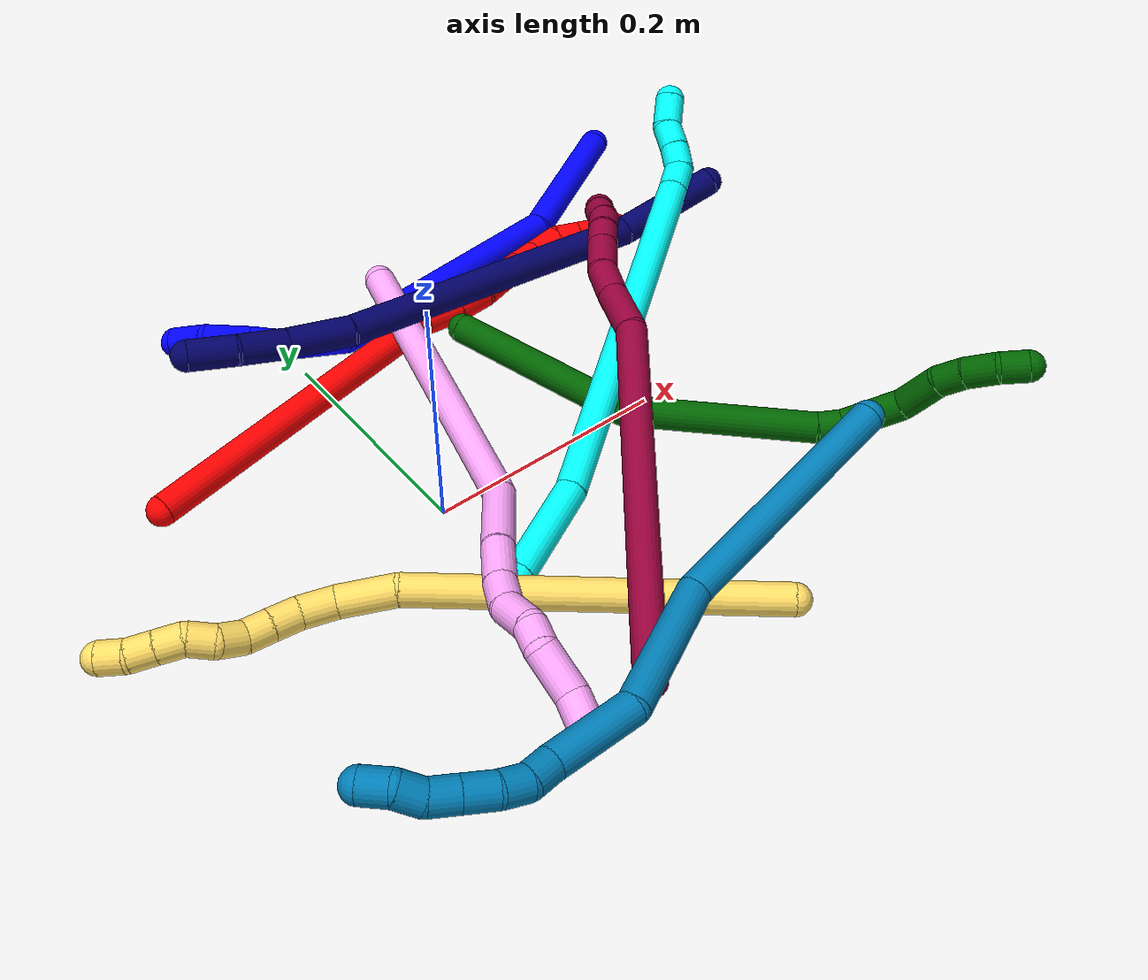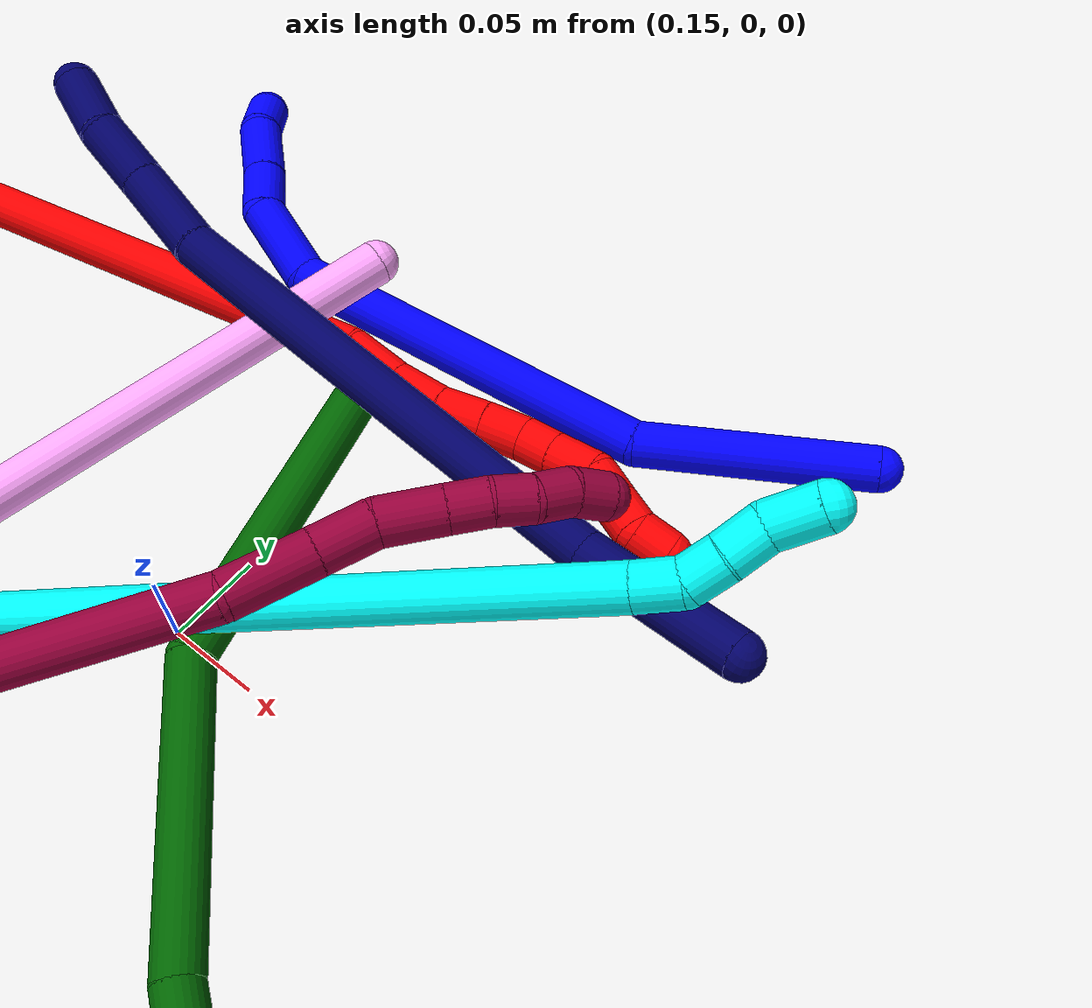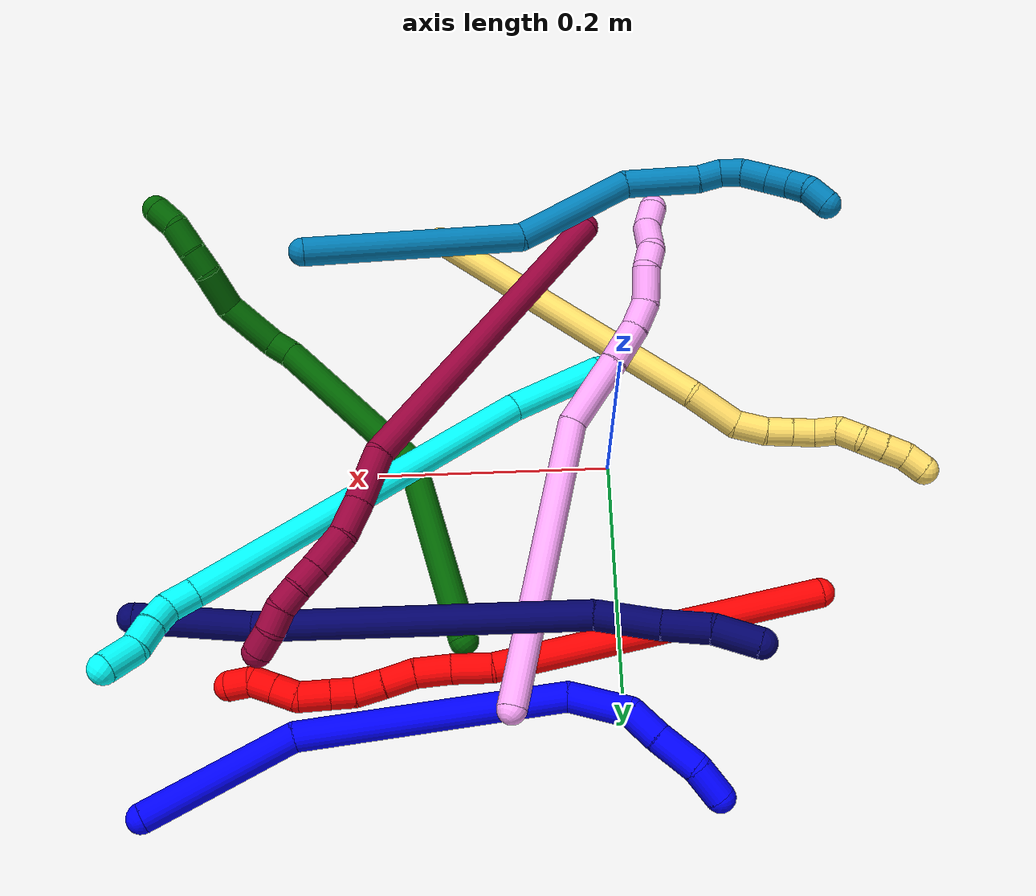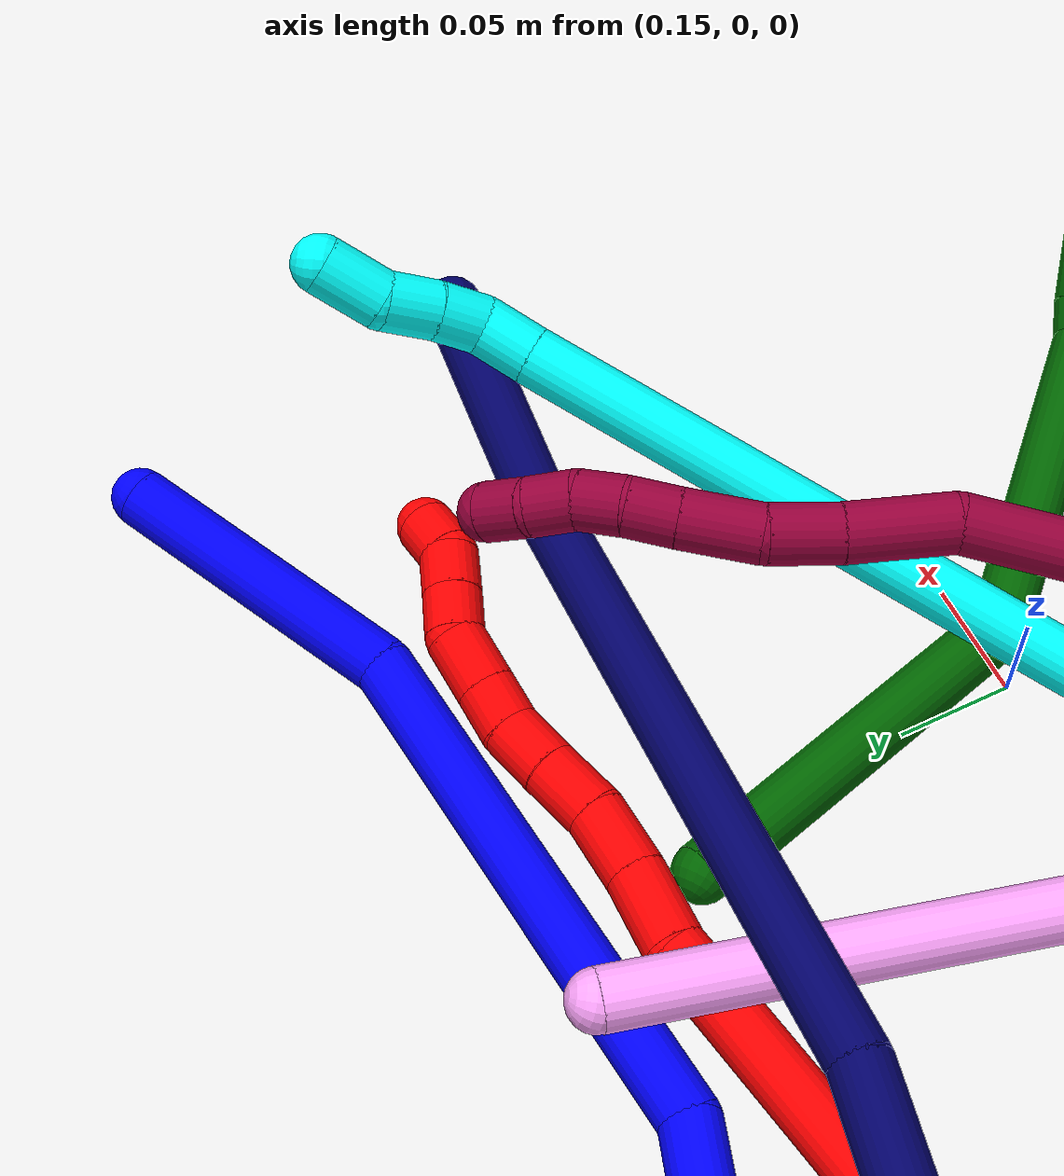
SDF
<sdf version="1.7">
 <world name="default">
  <plugin name="TubeGeneratorPlugin" filename="libtube_generator_plugin.so"/>
  <model name="photoneo_s_sensor">
   <static>1</static>
   <pose>0 0 2 1.57079 1.57079 3.14159</pose>
   <link name="link">
    <inertial><mass>0.1</mass></inertial>
    <sensor name="sensor" type="depth">
     <update_rate>30</update_rate>
     <camera>
      <horizontal_fov>1.22</horizontal_fov>
      <image><width>1920</width><height>1200</height><format>B8G8R8</format></image>
      <clip><near>0.1</near><far>4</far></clip>
      <depth_camera><output>points</output></depth_camera>
     </camera>
     <plugin name="camera_plugin" filename="libgazebo_ros_depth_camera.so">
      <baseline>0.2</baseline>
      <alwaysOn>1</alwaysOn>
      <updateRate>0.0</updateRate>
      <cameraName>camera_ir</cameraName>
      <imageTopicName>/camera/color/image_raw</imageTopicName>
      <cameraInfoTopicName>/camera/color/camera_info</cameraInfoTopicName>
      <depthImageTopicName>/camera/depth/image_raw</depthImageTopicName>
      <depthImageCameraInfoTopicName>/camera/depth/camera_info</depthImageCameraInfoTopicName>
      <pointCloudTopicName>/camera/depth/points</pointCloudTopicName>
      <frameName>fr_optical</frameName>
      <pointCloudCutoff>0.1</pointCloudCutoff>
      <pointCloudCutoffMax>2.0</pointCloudCutoffMax>
      <distortionK1>0</distortionK1>
      <distortionK2>0</distortionK2>
      <distortionK3>0</distortionK3>
      <distortionT1>0</distortionT1>
      <distortionT2>0</distortionT2>
      <CxPrime>0</CxPrime>
      <Cx>0</Cx>
      <Cy>0</Cy>
      <focalLength>0</focalLength>
      <hackBaseline>0</hackBaseline>
     </plugin>
    </sensor>
   </link>
  </model>
  <gravity>0 0 -9.8</gravity>
  <magnetic_field>6e-06 2.3e-05 -4.2e-05</magnetic_field>
  <atmosphere type="adiabatic"/>
  <physics name="default_physics" default="0" type="ode">
   <max_step_size>0.003</max_step_size>
   <real_time_factor>1</real_time_factor>
   <real_time_update_rate>1000</real_time_update_rate>
   <max_contacts>10000</max_contacts>
   <ode>
    <solver>
     <type>quick</type>
     <iters>100</iters>
     <sor>1.3</sor>
     <use_dynamic_moi_rescaling>0</use_dynamic_moi_rescaling>
    </solver>
    <constraints>
     <contact_max_correcting_vel>0</contact_max_correcting_vel>
     <contact_surface_layer>0.001</contact_surface_layer>
     <cfm>0</cfm>
     <erp>0.2</erp>
    </constraints>
   </ode>
  </physics>
  <scene><ambient>0.4 0.4 0.4 1</ambient><background>0.7 0.7 0.7 1</background><shadows>0</shadows></scene>
  <audio><device>default</device></audio>
  <spherical_coordinates>
   <surface_model>EARTH_WGS84</surface_model>
   <latitude_deg>0</latitude_deg>
   <longitude_deg>0</longitude_deg>
   <elevation>0</elevation>
   <heading_deg>0</heading_deg>
  </spherical_coordinates>
  <model name="bin">
   <static>1</static>
   <link name="bottom">
    <collision name="collision-bottom">
     <pose>0 0 -0.01 0 -0 0</pose>
     <geometry><box><size>0.8 0.6 0.02</size></box></geometry>
     <surface>
      <friction><ode><mu>100</mu><mu2>100</mu2></ode></friction>
      <contact><collide_bitmask>65535</collide_bitmask></contact>
     </surface>
    </collision>
   </link>
   <link name="west_wall">
    <collision name="collision-west_wall">
     <pose>-0.41 0 0.1 0 -0 0</pose>
     <geometry><box><size>0.02 0.6 0.2</size></box></geometry>
     <surface>
      <friction><ode><mu>100</mu><mu2>100</mu2></ode></friction>
      <contact><collide_bitmask>65535</collide_bitmask></contact>
     </surface>
    </collision>
   </link>
   <link name="east_wall">
    <collision name="collision-east_wall">
     <pose>0.41 0 0.1 0 -0 0</pose>
     <geometry><box><size>0.02 0.6 0.2</size></box></geometry>
     <surface>
      <friction><ode><mu>100</mu><mu2>100</mu2></ode></friction>
      <contact><collide_bitmask>65535</collide_bitmask></contact>
     </surface>
    </collision>
   </link>
   <link name="south_wall">
    <collision name="collision-south_wall">
     <pose>0 -0.31 0.1 0 -0 0</pose>
     <geometry><box><size>0.8 0.02 0.2</size></box></geometry>
     <surface>
      <friction><ode><mu>100</mu><mu2>100</mu2></ode></friction>
      <contact><collide_bitmask>65535</collide_bitmask></contact>
     </surface>
    </collision>
   </link>
   <link name="north_wall">
    <collision name="collision-north_wall">
     <pose>0 0.31 0.1 0 -0 0</pose>
     <geometry><box><size>0.8 0.02 0.2</size></box></geometry>
     <surface>
      <friction><ode><mu>100</mu><mu2>100</mu2></ode></friction>
      <contact><collide_bitmask>65535</collide_bitmask></contact>
     </surface>
    </collision>
   </link>
  </model>
  <model name="1">
   <static>0</static>
   <link name="1">
    <collision name="collision-cylinder-e_1_1_4">
     <pose>0.015218 0.031046 0.054394 -0.518642 0.238366 -0.063517</pose>
     <geometry><cylinder><radius>0.0125</radius><length>0.128906</length></cylinder></geometry>
     <surface>
      <friction><ode><mu>1.16</mu><mu2>1.16</mu2><slip1>0</slip1><slip2>0</slip2></ode></friction>
      <contact><ode><kp>1e+06</kp><kd>1</kd><max_vel>0</max_vel><min_depth>0.001</min_depth></ode></contact>
     </surface>
    </collision>
    <visual name="visual-cylinder-e_1_1_4">
     <pose>0.015218 0.031046 0.054394 -0.518642 0.238366 -0.063517</pose>
     <geometry><cylinder><radius>0.0125</radius><length>0.128906</length></cylinder></geometry>
     <material><ambient>0 0 1 1</ambient></material>
    </visual>
    <collision name="collision-cylinder-e_2_4_5">
     <pose>0.034486 0.145693 0.181598 -0.854282 0.036511 -0.01662</pose>
     <geometry><cylinder><radius>0.0125</radius><length>0.221871</length></cylinder></geometry>
     <surface>
      <friction><ode><mu>1.16</mu><mu2>1.16</mu2><slip1>0</slip1><slip2>0</slip2></ode></friction>
      <contact><ode><kp>1e+06</kp><kd>1</kd><max_vel>0</max_vel><min_depth>0.001</min_depth></ode></contact>
     </surface>
    </collision>
    <visual name="visual-cylinder-e_2_4_5">
     <pose>0.034486 0.145693 0.181598 -0.854282 0.036511 -0.01662</pose>
     <geometry><cylinder><radius>0.0125</radius><length>0.221871</length></cylinder></geometry>
     <material><ambient>0 0 1 1</ambient></material>
    </visual>
    <collision name="collision-cylinder-e_3_5_6">
     <pose>0.034801 0.254034 0.261956 -1.27466 -0.14337 0.106234</pose>
     <geometry><cylinder><radius>0.0125</radius><length>0.052269</length></cylinder></geometry>
     <surface>
      <friction><ode><mu>1.16</mu><mu2>1.16</mu2><slip1>0</slip1><slip2>0</slip2></ode></friction>
      <contact><ode><kp>1e+06</kp><kd>1</kd><max_vel>0</max_vel><min_depth>0.001</min_depth></ode></contact>
     </surface>
    </collision>
    <visual name="visual-cylinder-e_3_5_6">
     <pose>0.034801 0.254034 0.261956 -1.27466 -0.14337 0.106234</pose>
     <geometry><cylinder><radius>0.0125</radius><length>0.052269</length></cylinder></geometry>
     <material><ambient>0 0 1 1</ambient></material>
    </visual>
    <collision name="collision-cylinder-e_4_6_7">
     <pose>0.023458 0.291323 0.26916 -1.59819 -0.544969 0.559339</pose>
     <geometry><cylinder><radius>0.0125</radius><length>0.029359</length></cylinder></geometry>
     <surface>
      <friction><ode><mu>1.16</mu><mu2>1.16</mu2><slip1>0</slip1><slip2>0</slip2></ode></friction>
      <contact><ode><kp>1e+06</kp><kd>1</kd><max_vel>0</max_vel><min_depth>0.001</min_depth></ode></contact>
     </surface>
    </collision>
    <visual name="visual-cylinder-e_4_6_7">
     <pose>0.023458 0.291323 0.26916 -1.59819 -0.544969 0.559339</pose>
     <geometry><cylinder><radius>0.0125</radius><length>0.029359</length></cylinder></geometry>
     <material><ambient>0 0 1 1</ambient></material>
    </visual>
    <collision name="collision-cylinder-e_5_7_8">
     <pose>0.006668 0.320493 0.269751 -1.51465 -0.503941 0.477472</pose>
     <geometry><cylinder><radius>0.0125</radius><length>0.038024</length></cylinder></geometry>
     <surface>
      <friction><ode><mu>1.16</mu><mu2>1.16</mu2><slip1>0</slip1><slip2>0</slip2></ode></friction>
      <contact><ode><kp>1e+06</kp><kd>1</kd><max_vel>0</max_vel><min_depth>0.001</min_depth></ode></contact>
     </surface>
    </collision>
    <visual name="visual-cylinder-e_5_7_8">
     <pose>0.006668 0.320493 0.269751 -1.51465 -0.503941 0.477472</pose>
     <geometry><cylinder><radius>0.0125</radius><length>0.038024</length></cylinder></geometry>
     <material><ambient>0 0 1 1</ambient></material>
    </visual>
    <collision name="collision-cylinder-e_6_8_2">
     <pose>-0.013778 0.34661 0.271936 -1.43979 -0.866258 0.770446</pose>
     <geometry><cylinder><radius>0.0125</radius><length>0.029572</length></cylinder></geometry>
     <surface>
      <friction><ode><mu>1.16</mu><mu2>1.16</mu2><slip1>0</slip1><slip2>0</slip2></ode></friction>
      <contact><ode><kp>1e+06</kp><kd>1</kd><max_vel>0</max_vel><min_depth>0.001</min_depth></ode></contact>
     </surface>
    </collision>
    <visual name="visual-cylinder-e_6_8_2">
     <pose>-0.013778 0.34661 0.271936 -1.43979 -0.866258 0.770446</pose>
     <geometry><cylinder><radius>0.0125</radius><length>0.029572</length></cylinder></geometry>
     <material><ambient>0 0 1 1</ambient></material>
    </visual>
    <collision name="collision-sphere-2">
     <pose>-0.025044 0.356104 0.273187 0 -0 0</pose>
     <geometry><sphere><radius>0.0125</radius></sphere></geometry>
     <surface>
      <friction><ode><mu>1.16</mu><mu2>1.16</mu2><slip1>0</slip1><slip2>0</slip2></ode></friction>
      <contact><ode><kp>1e+06</kp><kd>1</kd><max_vel>0</max_vel><min_depth>0.001</min_depth></ode></contact>
     </surface>
    </collision>
    <visual name="visual-sphere-2">
     <pose>-0.025044 0.356104 0.273187 0 -0 0</pose>
     <geometry><sphere><radius>0.0125</radius></sphere></geometry>
     <material><ambient>0 0 1 1</ambient></material>
    </visual>
    <collision name="collision-sphere-4">
     <pose>0.030437 0.062092 0.108788 0 -0 0</pose>
     <geometry><sphere><radius>0.0125</radius></sphere></geometry>
     <surface>
      <friction><ode><mu>1.16</mu><mu2>1.16</mu2><slip1>0</slip1><slip2>0</slip2></ode></friction>
      <contact><ode><kp>1e+06</kp><kd>1</kd><max_vel>0</max_vel><min_depth>0.001</min_depth></ode></contact>
     </surface>
    </collision>
    <visual name="visual-sphere-4">
     <pose>0.030437 0.062092 0.108788 0 -0 0</pose>
     <geometry><sphere><radius>0.0125</radius></sphere></geometry>
     <material><ambient>0 0 1 1</ambient></material>
    </visual>
    <collision name="collision-sphere-1">
     <geometry><sphere><radius>0.0125</radius></sphere></geometry>
     <surface>
      <friction><ode><mu>1.16</mu><mu2>1.16</mu2><slip1>0</slip1><slip2>0</slip2></ode></friction>
      <contact><ode><kp>1e+06</kp><kd>1</kd><max_vel>0</max_vel><min_depth>0.001</min_depth></ode></contact>
     </surface>
    </collision>
    <visual name="visual-sphere-1">
     <geometry><sphere><radius>0.0125</radius></sphere></geometry>
     <material><ambient>0 0 1 1</ambient></material>
    </visual>
    <collision name="collision-sphere-8">
     <pose>-0.002513 0.337115 0.270685 0 -0 0</pose>
     <geometry><sphere><radius>0.0125</radius></sphere></geometry>
     <surface>
      <friction><ode><mu>1.16</mu><mu2>1.16</mu2><slip1>0</slip1><slip2>0</slip2></ode></friction>
      <contact><ode><kp>1e+06</kp><kd>1</kd><max_vel>0</max_vel><min_depth>0.001</min_depth></ode></contact>
     </surface>
    </collision>
    <visual name="visual-sphere-8">
     <pose>-0.002513 0.337115 0.270685 0 -0 0</pose>
     <geometry><sphere><radius>0.0125</radius></sphere></geometry>
     <material><ambient>0 0 1 1</ambient></material>
    </visual>
    <collision name="collision-sphere-5">
     <pose>0.038536 0.229293 0.254407 0 -0 0</pose>
     <geometry><sphere><radius>0.0125</radius></sphere></geometry>
     <surface>
      <friction><ode><mu>1.16</mu><mu2>1.16</mu2><slip1>0</slip1><slip2>0</slip2></ode></friction>
      <contact><ode><kp>1e+06</kp><kd>1</kd><max_vel>0</max_vel><min_depth>0.001</min_depth></ode></contact>
     </surface>
    </collision>
    <visual name="visual-sphere-5">
     <pose>0.038536 0.229293 0.254407 0 -0 0</pose>
     <geometry><sphere><radius>0.0125</radius></sphere></geometry>
     <material><ambient>0 0 1 1</ambient></material>
    </visual>
    <collision name="collision-sphere-6">
     <pose>0.031067 0.278774 0.269504 0 -0 0</pose>
     <geometry><sphere><radius>0.0125</radius></sphere></geometry>
     <surface>
      <friction><ode><mu>1.16</mu><mu2>1.16</mu2><slip1>0</slip1><slip2>0</slip2></ode></friction>
      <contact><ode><kp>1e+06</kp><kd>1</kd><max_vel>0</max_vel><min_depth>0.001</min_depth></ode></contact>
     </surface>
    </collision>
    <visual name="visual-sphere-6">
     <pose>0.031067 0.278774 0.269504 0 -0 0</pose>
     <geometry><sphere><radius>0.0125</radius></sphere></geometry>
     <material><ambient>0 0 1 1</ambient></material>
    </visual>
    <collision name="collision-sphere-7">
     <pose>0.015848 0.303871 0.268817 0 -0 0</pose>
     <geometry><sphere><radius>0.0125</radius></sphere></geometry>
     <surface>
      <friction><ode><mu>1.16</mu><mu2>1.16</mu2><slip1>0</slip1><slip2>0</slip2></ode></friction>
      <contact><ode><kp>1e+06</kp><kd>1</kd><max_vel>0</max_vel><min_depth>0.001</min_depth></ode></contact>
     </surface>
    </collision>
    <visual name="visual-sphere-7">
     <pose>0.015848 0.303871 0.268817 0 -0 0</pose>
     <geometry><sphere><radius>0.0125</radius></sphere></geometry>
     <material><ambient>0 0 1 1</ambient></material>
    </visual>
    <inertial>
     <pose>0.023934 0.161188 0.174392 0 -0 0</pose>
     <mass>0.5</mass>
     <inertia>
      <ixx>0.001097</ixx>
      <ixy>0</ixy>
      <ixz>0</ixz>
      <iyy>0.000781</iyy>
      <iyz>0</iyz>
      <izz>-0.000851</izz>
     </inertia>
    </inertial>
   </link>
   <pose>0.378536 0.2885 0.022335 2.4616 -0.795562 -1.5135</pose>
  </model>
  <model name="2">
   <static>0</static>
   <link name="2">
    <collision name="collision-cylinder-e_1_1_4">
     <pose>0.026094 0.017193 0.136224 -0.125545 0.187805 -0.011839</pose>
     <geometry><cylinder><radius>0.0125</radius><length>0.279525</length></cylinder></geometry>
     <surface>
      <friction><ode><mu>1.16</mu><mu2>1.16</mu2><slip1>0</slip1><slip2>0</slip2></ode></friction>
      <contact><ode><kp>1e+06</kp><kd>1</kd><max_vel>0</max_vel><min_depth>0.001</min_depth></ode></contact>
     </surface>
    </collision>
    <visual name="visual-cylinder-e_1_1_4">
     <pose>0.026094 0.017193 0.136224 -0.125545 0.187805 -0.011839</pose>
     <geometry><cylinder><radius>0.0125</radius><length>0.279525</length></cylinder></geometry>
     <material><ambient>1 0 0 1</ambient></material>
    </visual>
    <collision name="collision-cylinder-e_2_4_5">
     <pose>0.054935 0.040438 0.288042 -0.370264 0.16274 -0.030542</pose>
     <geometry><cylinder><radius>0.0125</radius><length>0.033901</length></cylinder></geometry>
     <surface>
      <friction><ode><mu>1.16</mu><mu2>1.16</mu2><slip1>0</slip1><slip2>0</slip2></ode></friction>
      <contact><ode><kp>1e+06</kp><kd>1</kd><max_vel>0</max_vel><min_depth>0.001</min_depth></ode></contact>
     </surface>
    </collision>
    <visual name="visual-cylinder-e_2_4_5">
     <pose>0.054935 0.040438 0.288042 -0.370264 0.16274 -0.030542</pose>
     <geometry><cylinder><radius>0.0125</radius><length>0.033901</length></cylinder></geometry>
     <material><ambient>1 0 0 1</ambient></material>
    </visual>
    <collision name="collision-cylinder-e_3_5_6">
     <pose>0.060716 0.050164 0.317963 -0.250965 0.202411 -0.025619</pose>
     <geometry><cylinder><radius>0.0125</radius><length>0.030199</length></cylinder></geometry>
     <surface>
      <friction><ode><mu>1.16</mu><mu2>1.16</mu2><slip1>0</slip1><slip2>0</slip2></ode></friction>
      <contact><ode><kp>1e+06</kp><kd>1</kd><max_vel>0</max_vel><min_depth>0.001</min_depth></ode></contact>
     </surface>
    </collision>
    <visual name="visual-cylinder-e_3_5_6">
     <pose>0.060716 0.050164 0.317963 -0.250965 0.202411 -0.025619</pose>
     <geometry><cylinder><radius>0.0125</radius><length>0.030199</length></cylinder></geometry>
     <material><ambient>1 0 0 1</ambient></material>
    </visual>
    <collision name="collision-cylinder-e_4_6_7">
     <pose>0.065361 0.054459 0.345403 -0.047364 0.121946 -0.002892</pose>
     <geometry><cylinder><radius>0.0125</radius><length>0.02645</length></cylinder></geometry>
     <surface>
      <friction><ode><mu>1.16</mu><mu2>1.16</mu2><slip1>0</slip1><slip2>0</slip2></ode></friction>
      <contact><ode><kp>1e+06</kp><kd>1</kd><max_vel>0</max_vel><min_depth>0.001</min_depth></ode></contact>
     </surface>
    </collision>
    <visual name="visual-cylinder-e_4_6_7">
     <pose>0.065361 0.054459 0.345403 -0.047364 0.121946 -0.002892</pose>
     <geometry><cylinder><radius>0.0125</radius><length>0.02645</length></cylinder></geometry>
     <material><ambient>1 0 0 1</ambient></material>
    </visual>
    <collision name="collision-cylinder-e_5_7_8">
     <pose>0.068283 0.056114 0.370339 -0.087189 0.110259 -0.004815</pose>
     <geometry><cylinder><radius>0.0125</radius><length>0.023884</length></cylinder></geometry>
     <surface>
      <friction><ode><mu>1.16</mu><mu2>1.16</mu2><slip1>0</slip1><slip2>0</slip2></ode></friction>
      <contact><ode><kp>1e+06</kp><kd>1</kd><max_vel>0</max_vel><min_depth>0.001</min_depth></ode></contact>
     </surface>
    </collision>
    <visual name="visual-cylinder-e_5_7_8">
     <pose>0.068283 0.056114 0.370339 -0.087189 0.110259 -0.004815</pose>
     <geometry><cylinder><radius>0.0125</radius><length>0.023884</length></cylinder></geometry>
     <material><ambient>1 0 0 1</ambient></material>
    </visual>
    <collision name="collision-cylinder-e_6_8_9">
     <pose>0.072613 0.059299 0.391457 -0.227486 0.306194 -0.035251</pose>
     <geometry><cylinder><radius>0.0125</radius><length>0.02001</length></cylinder></geometry>
     <surface>
      <friction><ode><mu>1.16</mu><mu2>1.16</mu2><slip1>0</slip1><slip2>0</slip2></ode></friction>
      <contact><ode><kp>1e+06</kp><kd>1</kd><max_vel>0</max_vel><min_depth>0.001</min_depth></ode></contact>
     </surface>
    </collision>
    <visual name="visual-cylinder-e_6_8_9">
     <pose>0.072613 0.059299 0.391457 -0.227486 0.306194 -0.035251</pose>
     <geometry><cylinder><radius>0.0125</radius><length>0.02001</length></cylinder></geometry>
     <material><ambient>1 0 0 1</ambient></material>
    </visual>
    <collision name="collision-cylinder-e_7_9_10">
     <pose>0.07966 0.064054 0.412727 -0.214036 0.317714 -0.034418</pose>
     <geometry><cylinder><radius>0.0125</radius><length>0.025804</length></cylinder></geometry>
     <surface>
      <friction><ode><mu>1.16</mu><mu2>1.16</mu2><slip1>0</slip1><slip2>0</slip2></ode></friction>
      <contact><ode><kp>1e+06</kp><kd>1</kd><max_vel>0</max_vel><min_depth>0.001</min_depth></ode></contact>
     </surface>
    </collision>
    <visual name="visual-cylinder-e_7_9_10">
     <pose>0.07966 0.064054 0.412727 -0.214036 0.317714 -0.034418</pose>
     <geometry><cylinder><radius>0.0125</radius><length>0.025804</length></cylinder></geometry>
     <material><ambient>1 0 0 1</ambient></material>
    </visual>
    <collision name="collision-cylinder-e_8_10_11">
     <pose>0.086795 0.072843 0.43199 -0.703953 0.314102 -0.116187</pose>
     <geometry><cylinder><radius>0.0125</radius><length>0.020099</length></cylinder></geometry>
     <surface>
      <friction><ode><mu>1.16</mu><mu2>1.16</mu2><slip1>0</slip1><slip2>0</slip2></ode></friction>
      <contact><ode><kp>1e+06</kp><kd>1</kd><max_vel>0</max_vel><min_depth>0.001</min_depth></ode></contact>
     </surface>
    </collision>
    <visual name="visual-cylinder-e_8_10_11">
     <pose>0.086795 0.072843 0.43199 -0.703953 0.314102 -0.116187</pose>
     <geometry><cylinder><radius>0.0125</radius><length>0.020099</length></cylinder></geometry>
     <material><ambient>1 0 0 1</ambient></material>
    </visual>
    <collision name="collision-cylinder-e_9_11_12">
     <pose>0.092972 0.085083 0.446663 -0.686479 0.311233 -0.11202</pose>
     <geometry><cylinder><radius>0.0125</radius><length>0.020066</length></cylinder></geometry>
     <surface>
      <friction><ode><mu>1.16</mu><mu2>1.16</mu2><slip1>0</slip1><slip2>0</slip2></ode></friction>
      <contact><ode><kp>1e+06</kp><kd>1</kd><max_vel>0</max_vel><min_depth>0.001</min_depth></ode></contact>
     </surface>
    </collision>
    <visual name="visual-cylinder-e_9_11_12">
     <pose>0.092972 0.085083 0.446663 -0.686479 0.311233 -0.11202</pose>
     <geometry><cylinder><radius>0.0125</radius><length>0.020066</length></cylinder></geometry>
     <material><ambient>1 0 0 1</ambient></material>
    </visual>
    <collision name="collision-cylinder-e_10_12_2">
     <pose>0.095841 0.094093 0.463634 -0.2992 -0.020333 0.003065</pose>
     <geometry><cylinder><radius>0.0125</radius><length>0.020062</length></cylinder></geometry>
     <surface>
      <friction><ode><mu>1.16</mu><mu2>1.16</mu2><slip1>0</slip1><slip2>0</slip2></ode></friction>
      <contact><ode><kp>1e+06</kp><kd>1</kd><max_vel>0</max_vel><min_depth>0.001</min_depth></ode></contact>
     </surface>
    </collision>
    <visual name="visual-cylinder-e_10_12_2">
     <pose>0.095841 0.094093 0.463634 -0.2992 -0.020333 0.003065</pose>
     <geometry><cylinder><radius>0.0125</radius><length>0.020062</length></cylinder></geometry>
     <material><ambient>1 0 0 1</ambient></material>
    </visual>
    <collision name="collision-sphere-2">
     <pose>0.095637 0.097049 0.473218 0 -0 0</pose>
     <geometry><sphere><radius>0.0125</radius></sphere></geometry>
     <surface>
      <friction><ode><mu>1.16</mu><mu2>1.16</mu2><slip1>0</slip1><slip2>0</slip2></ode></friction>
      <contact><ode><kp>1e+06</kp><kd>1</kd><max_vel>0</max_vel><min_depth>0.001</min_depth></ode></contact>
     </surface>
    </collision>
    <visual name="visual-sphere-2">
     <pose>0.095637 0.097049 0.473218 0 -0 0</pose>
     <geometry><sphere><radius>0.0125</radius></sphere></geometry>
     <material><ambient>1 0 0 1</ambient></material>
    </visual>
    <collision name="collision-sphere-12">
     <pose>0.096045 0.091136 0.454051 0 -0 0</pose>
     <geometry><sphere><radius>0.0125</radius></sphere></geometry>
     <surface>
      <friction><ode><mu>1.16</mu><mu2>1.16</mu2><slip1>0</slip1><slip2>0</slip2></ode></friction>
      <contact><ode><kp>1e+06</kp><kd>1</kd><max_vel>0</max_vel><min_depth>0.001</min_depth></ode></contact>
     </surface>
    </collision>
    <visual name="visual-sphere-12">
     <pose>0.096045 0.091136 0.454051 0 -0 0</pose>
     <geometry><sphere><radius>0.0125</radius></sphere></geometry>
     <material><ambient>1 0 0 1</ambient></material>
    </visual>
    <collision name="collision-sphere-11">
     <pose>0.0899 0.079029 0.439275 0 -0 0</pose>
     <geometry><sphere><radius>0.0125</radius></sphere></geometry>
     <surface>
      <friction><ode><mu>1.16</mu><mu2>1.16</mu2><slip1>0</slip1><slip2>0</slip2></ode></friction>
      <contact><ode><kp>1e+06</kp><kd>1</kd><max_vel>0</max_vel><min_depth>0.001</min_depth></ode></contact>
     </surface>
    </collision>
    <visual name="visual-sphere-11">
     <pose>0.0899 0.079029 0.439275 0 -0 0</pose>
     <geometry><sphere><radius>0.0125</radius></sphere></geometry>
     <material><ambient>1 0 0 1</ambient></material>
    </visual>
    <collision name="collision-sphere-10">
     <pose>0.08369 0.066657 0.424704 0 -0 0</pose>
     <geometry><sphere><radius>0.0125</radius></sphere></geometry>
     <surface>
      <friction><ode><mu>1.16</mu><mu2>1.16</mu2><slip1>0</slip1><slip2>0</slip2></ode></friction>
      <contact><ode><kp>1e+06</kp><kd>1</kd><max_vel>0</max_vel><min_depth>0.001</min_depth></ode></contact>
     </surface>
    </collision>
    <visual name="visual-sphere-10">
     <pose>0.08369 0.066657 0.424704 0 -0 0</pose>
     <geometry><sphere><radius>0.0125</radius></sphere></geometry>
     <material><ambient>1 0 0 1</ambient></material>
    </visual>
    <collision name="collision-sphere-9">
     <pose>0.075629 0.06145 0.400751 0 -0 0</pose>
     <geometry><sphere><radius>0.0125</radius></sphere></geometry>
     <surface>
      <friction><ode><mu>1.16</mu><mu2>1.16</mu2><slip1>0</slip1><slip2>0</slip2></ode></friction>
      <contact><ode><kp>1e+06</kp><kd>1</kd><max_vel>0</max_vel><min_depth>0.001</min_depth></ode></contact>
     </surface>
    </collision>
    <visual name="visual-sphere-9">
     <pose>0.075629 0.06145 0.400751 0 -0 0</pose>
     <geometry><sphere><radius>0.0125</radius></sphere></geometry>
     <material><ambient>1 0 0 1</ambient></material>
    </visual>
    <collision name="collision-sphere-4">
     <pose>0.052188 0.034385 0.272449 0 -0 0</pose>
     <geometry><sphere><radius>0.0125</radius></sphere></geometry>
     <surface>
      <friction><ode><mu>1.16</mu><mu2>1.16</mu2><slip1>0</slip1><slip2>0</slip2></ode></friction>
      <contact><ode><kp>1e+06</kp><kd>1</kd><max_vel>0</max_vel><min_depth>0.001</min_depth></ode></contact>
     </surface>
    </collision>
    <visual name="visual-sphere-4">
     <pose>0.052188 0.034385 0.272449 0 -0 0</pose>
     <geometry><sphere><radius>0.0125</radius></sphere></geometry>
     <material><ambient>1 0 0 1</ambient></material>
    </visual>
    <collision name="collision-sphere-1">
     <geometry><sphere><radius>0.0125</radius></sphere></geometry>
     <surface>
      <friction><ode><mu>1.16</mu><mu2>1.16</mu2><slip1>0</slip1><slip2>0</slip2></ode></friction>
      <contact><ode><kp>1e+06</kp><kd>1</kd><max_vel>0</max_vel><min_depth>0.001</min_depth></ode></contact>
     </surface>
    </collision>
    <visual name="visual-sphere-1">
     <geometry><sphere><radius>0.0125</radius></sphere></geometry>
     <material><ambient>1 0 0 1</ambient></material>
    </visual>
    <collision name="collision-sphere-8">
     <pose>0.069597 0.057147 0.382163 0 -0 0</pose>
     <geometry><sphere><radius>0.0125</radius></sphere></geometry>
     <surface>
      <friction><ode><mu>1.16</mu><mu2>1.16</mu2><slip1>0</slip1><slip2>0</slip2></ode></friction>
      <contact><ode><kp>1e+06</kp><kd>1</kd><max_vel>0</max_vel><min_depth>0.001</min_depth></ode></contact>
     </surface>
    </collision>
    <visual name="visual-sphere-8">
     <pose>0.069597 0.057147 0.382163 0 -0 0</pose>
     <geometry><sphere><radius>0.0125</radius></sphere></geometry>
     <material><ambient>1 0 0 1</ambient></material>
    </visual>
    <collision name="collision-sphere-5">
     <pose>0.057681 0.046491 0.303635 0 -0 0</pose>
     <geometry><sphere><radius>0.0125</radius></sphere></geometry>
     <surface>
      <friction><ode><mu>1.16</mu><mu2>1.16</mu2><slip1>0</slip1><slip2>0</slip2></ode></friction>
      <contact><ode><kp>1e+06</kp><kd>1</kd><max_vel>0</max_vel><min_depth>0.001</min_depth></ode></contact>
     </surface>
    </collision>
    <visual name="visual-sphere-5">
     <pose>0.057681 0.046491 0.303635 0 -0 0</pose>
     <geometry><sphere><radius>0.0125</radius></sphere></geometry>
     <material><ambient>1 0 0 1</ambient></material>
    </visual>
    <collision name="collision-sphere-6">
     <pose>0.063752 0.053837 0.332291 0 -0 0</pose>
     <geometry><sphere><radius>0.0125</radius></sphere></geometry>
     <surface>
      <friction><ode><mu>1.16</mu><mu2>1.16</mu2><slip1>0</slip1><slip2>0</slip2></ode></friction>
      <contact><ode><kp>1e+06</kp><kd>1</kd><max_vel>0</max_vel><min_depth>0.001</min_depth></ode></contact>
     </surface>
    </collision>
    <visual name="visual-sphere-6">
     <pose>0.063752 0.053837 0.332291 0 -0 0</pose>
     <geometry><sphere><radius>0.0125</radius></sphere></geometry>
     <material><ambient>1 0 0 1</ambient></material>
    </visual>
    <collision name="collision-sphere-7">
     <pose>0.066969 0.05508 0.358514 0 -0 0</pose>
     <geometry><sphere><radius>0.0125</radius></sphere></geometry>
     <surface>
      <friction><ode><mu>1.16</mu><mu2>1.16</mu2><slip1>0</slip1><slip2>0</slip2></ode></friction>
      <contact><ode><kp>1e+06</kp><kd>1</kd><max_vel>0</max_vel><min_depth>0.001</min_depth></ode></contact>
     </surface>
    </collision>
    <visual name="visual-sphere-7">
     <pose>0.066969 0.05508 0.358514 0 -0 0</pose>
     <geometry><sphere><radius>0.0125</radius></sphere></geometry>
     <material><ambient>1 0 0 1</ambient></material>
    </visual>
    <inertial>
     <pose>0.046782 0.036741 0.241712 0 -0 0</pose>
     <mass>0.5</mass>
     <inertia>
      <ixx>0.001805</ixx>
      <ixy>0</ixy>
      <ixz>0</ixz>
      <iyy>0.001822</iyy>
      <iyz>0</iyz>
      <izz>-0.00054</izz>
     </inertia>
    </inertial>
   </link>
   <pose>-0.169666 0.124329 0.011497 -1.90869 -1.20404 -0.877311</pose>
  </model>
  <model name="3">
   <static>0</static>
   <link name="3">
    <collision name="collision-cylinder-e_1_1_4">
     <pose>0.021107 -0.000477 0.037398 0.012752 0.513782 0.00335</pose>
     <geometry><cylinder><radius>0.0125</radius><length>0.085892</length></cylinder></geometry>
     <surface>
      <friction><ode><mu>1.16</mu><mu2>1.16</mu2><slip1>0</slip1><slip2>0</slip2></ode></friction>
      <contact><ode><kp>1e+06</kp><kd>1</kd><max_vel>0</max_vel><min_depth>0.001</min_depth></ode></contact>
     </surface>
    </collision>
    <visual name="visual-cylinder-e_1_1_4">
     <pose>0.021107 -0.000477 0.037398 0.012752 0.513782 0.00335</pose>
     <geometry><cylinder><radius>0.0125</radius><length>0.085892</length></cylinder></geometry>
     <material><ambient>0.003922 1 0.996078 1</ambient></material>
    </visual>
    <collision name="collision-cylinder-e_2_4_5">
     <pose>0.100635 -0.029071 0.220138 0.191095 0.375879 0.03645</pose>
     <geometry><cylinder><radius>0.0125</radius><length>0.318293</length></cylinder></geometry>
     <surface>
      <friction><ode><mu>1.16</mu><mu2>1.16</mu2><slip1>0</slip1><slip2>0</slip2></ode></friction>
      <contact><ode><kp>1e+06</kp><kd>1</kd><max_vel>0</max_vel><min_depth>0.001</min_depth></ode></contact>
     </surface>
    </collision>
    <visual name="visual-cylinder-e_2_4_5">
     <pose>0.100635 -0.029071 0.220138 0.191095 0.375879 0.03645</pose>
     <geometry><cylinder><radius>0.0125</radius><length>0.318293</length></cylinder></geometry>
     <material><ambient>0.003922 1 0.996078 1</ambient></material>
    </visual>
    <collision name="collision-cylinder-e_3_5_6">
     <pose>0.163529 -0.060107 0.376245 0.264805 0.381324 0.051399</pose>
     <geometry><cylinder><radius>0.0125</radius><length>0.024037</length></cylinder></geometry>
     <surface>
      <friction><ode><mu>1.16</mu><mu2>1.16</mu2><slip1>0</slip1><slip2>0</slip2></ode></friction>
      <contact><ode><kp>1e+06</kp><kd>1</kd><max_vel>0</max_vel><min_depth>0.001</min_depth></ode></contact>
     </surface>
    </collision>
    <visual name="visual-cylinder-e_3_5_6">
     <pose>0.163529 -0.060107 0.376245 0.264805 0.381324 0.051399</pose>
     <geometry><cylinder><radius>0.0125</radius><length>0.024037</length></cylinder></geometry>
     <material><ambient>0.003922 1 0.996078 1</ambient></material>
    </visual>
    <collision name="collision-cylinder-e_4_6_7">
     <pose>0.167826 -0.068424 0.395913 0.54509 -0.016874 -0.004716</pose>
     <geometry><cylinder><radius>0.0125</radius><length>0.020822</length></cylinder></geometry>
     <surface>
      <friction><ode><mu>1.16</mu><mu2>1.16</mu2><slip1>0</slip1><slip2>0</slip2></ode></friction>
      <contact><ode><kp>1e+06</kp><kd>1</kd><max_vel>0</max_vel><min_depth>0.001</min_depth></ode></contact>
     </surface>
    </collision>
    <visual name="visual-cylinder-e_4_6_7">
     <pose>0.167826 -0.068424 0.395913 0.54509 -0.016874 -0.004716</pose>
     <geometry><cylinder><radius>0.0125</radius><length>0.020822</length></cylinder></geometry>
     <material><ambient>0.003922 1 0.996078 1</ambient></material>
    </visual>
    <collision name="collision-cylinder-e_5_7_8">
     <pose>0.166288 -0.079303 0.414682 0.50701 -0.120084 -0.031146</pose>
     <geometry><cylinder><radius>0.0125</radius><length>0.02274</length></cylinder></geometry>
     <surface>
      <friction><ode><mu>1.16</mu><mu2>1.16</mu2><slip1>0</slip1><slip2>0</slip2></ode></friction>
      <contact><ode><kp>1e+06</kp><kd>1</kd><max_vel>0</max_vel><min_depth>0.001</min_depth></ode></contact>
     </surface>
    </collision>
    <visual name="visual-cylinder-e_5_7_8">
     <pose>0.166288 -0.079303 0.414682 0.50701 -0.120084 -0.031146</pose>
     <geometry><cylinder><radius>0.0125</radius><length>0.02274</length></cylinder></geometry>
     <material><ambient>0.003922 1 0.996078 1</ambient></material>
    </visual>
    <collision name="collision-cylinder-e_6_8_2">
     <pose>0.168579 -0.091232 0.436555 0.492927 0.261894 0.066242</pose>
     <geometry><cylinder><radius>0.0125</radius><length>0.028215</length></cylinder></geometry>
     <surface>
      <friction><ode><mu>1.16</mu><mu2>1.16</mu2><slip1>0</slip1><slip2>0</slip2></ode></friction>
      <contact><ode><kp>1e+06</kp><kd>1</kd><max_vel>0</max_vel><min_depth>0.001</min_depth></ode></contact>
     </surface>
    </collision>
    <visual name="visual-cylinder-e_6_8_2">
     <pose>0.168579 -0.091232 0.436555 0.492927 0.261894 0.066242</pose>
     <geometry><cylinder><radius>0.0125</radius><length>0.028215</length></cylinder></geometry>
     <material><ambient>0.003922 1 0.996078 1</ambient></material>
    </visual>
    <collision name="collision-sphere-2">
     <pose>0.172231 -0.09768 0.448559 0 -0 0</pose>
     <geometry><sphere><radius>0.0125</radius></sphere></geometry>
     <surface>
      <friction><ode><mu>1.16</mu><mu2>1.16</mu2><slip1>0</slip1><slip2>0</slip2></ode></friction>
      <contact><ode><kp>1e+06</kp><kd>1</kd><max_vel>0</max_vel><min_depth>0.001</min_depth></ode></contact>
     </surface>
    </collision>
    <visual name="visual-sphere-2">
     <pose>0.172231 -0.09768 0.448559 0 -0 0</pose>
     <geometry><sphere><radius>0.0125</radius></sphere></geometry>
     <material><ambient>0.003922 1 0.996078 1</ambient></material>
    </visual>
    <collision name="collision-sphere-4">
     <pose>0.042214 -0.000954 0.074797 0 -0 0</pose>
     <geometry><sphere><radius>0.0125</radius></sphere></geometry>
     <surface>
      <friction><ode><mu>1.16</mu><mu2>1.16</mu2><slip1>0</slip1><slip2>0</slip2></ode></friction>
      <contact><ode><kp>1e+06</kp><kd>1</kd><max_vel>0</max_vel><min_depth>0.001</min_depth></ode></contact>
     </surface>
    </collision>
    <visual name="visual-sphere-4">
     <pose>0.042214 -0.000954 0.074797 0 -0 0</pose>
     <geometry><sphere><radius>0.0125</radius></sphere></geometry>
     <material><ambient>0.003922 1 0.996078 1</ambient></material>
    </visual>
    <collision name="collision-sphere-1">
     <geometry><sphere><radius>0.0125</radius></sphere></geometry>
     <surface>
      <friction><ode><mu>1.16</mu><mu2>1.16</mu2><slip1>0</slip1><slip2>0</slip2></ode></friction>
      <contact><ode><kp>1e+06</kp><kd>1</kd><max_vel>0</max_vel><min_depth>0.001</min_depth></ode></contact>
     </surface>
    </collision>
    <visual name="visual-sphere-1">
     <geometry><sphere><radius>0.0125</radius></sphere></geometry>
     <material><ambient>0.003922 1 0.996078 1</ambient></material>
    </visual>
    <collision name="collision-sphere-8">
     <pose>0.164926 -0.084784 0.42455 0 -0 0</pose>
     <geometry><sphere><radius>0.0125</radius></sphere></geometry>
     <surface>
      <friction><ode><mu>1.16</mu><mu2>1.16</mu2><slip1>0</slip1><slip2>0</slip2></ode></friction>
      <contact><ode><kp>1e+06</kp><kd>1</kd><max_vel>0</max_vel><min_depth>0.001</min_depth></ode></contact>
     </surface>
    </collision>
    <visual name="visual-sphere-8">
     <pose>0.164926 -0.084784 0.42455 0 -0 0</pose>
     <geometry><sphere><radius>0.0125</radius></sphere></geometry>
     <material><ambient>0.003922 1 0.996078 1</ambient></material>
    </visual>
    <collision name="collision-sphere-5">
     <pose>0.159056 -0.057188 0.365479 0 -0 0</pose>
     <geometry><sphere><radius>0.0125</radius></sphere></geometry>
     <surface>
      <friction><ode><mu>1.16</mu><mu2>1.16</mu2><slip1>0</slip1><slip2>0</slip2></ode></friction>
      <contact><ode><kp>1e+06</kp><kd>1</kd><max_vel>0</max_vel><min_depth>0.001</min_depth></ode></contact>
     </surface>
    </collision>
    <visual name="visual-sphere-5">
     <pose>0.159056 -0.057188 0.365479 0 -0 0</pose>
     <geometry><sphere><radius>0.0125</radius></sphere></geometry>
     <material><ambient>0.003922 1 0.996078 1</ambient></material>
    </visual>
    <collision name="collision-sphere-6">
     <pose>0.168001 -0.063027 0.387012 0 -0 0</pose>
     <geometry><sphere><radius>0.0125</radius></sphere></geometry>
     <surface>
      <friction><ode><mu>1.16</mu><mu2>1.16</mu2><slip1>0</slip1><slip2>0</slip2></ode></friction>
      <contact><ode><kp>1e+06</kp><kd>1</kd><max_vel>0</max_vel><min_depth>0.001</min_depth></ode></contact>
     </surface>
    </collision>
    <visual name="visual-sphere-6">
     <pose>0.168001 -0.063027 0.387012 0 -0 0</pose>
     <geometry><sphere><radius>0.0125</radius></sphere></geometry>
     <material><ambient>0.003922 1 0.996078 1</ambient></material>
    </visual>
    <collision name="collision-sphere-7">
     <pose>0.16765 -0.073822 0.404814 0 -0 0</pose>
     <geometry><sphere><radius>0.0125</radius></sphere></geometry>
     <surface>
      <friction><ode><mu>1.16</mu><mu2>1.16</mu2><slip1>0</slip1><slip2>0</slip2></ode></friction>
      <contact><ode><kp>1e+06</kp><kd>1</kd><max_vel>0</max_vel><min_depth>0.001</min_depth></ode></contact>
     </surface>
    </collision>
    <visual name="visual-sphere-7">
     <pose>0.16765 -0.073822 0.404814 0 -0 0</pose>
     <geometry><sphere><radius>0.0125</radius></sphere></geometry>
     <material><ambient>0.003922 1 0.996078 1</ambient></material>
    </visual>
    <inertial>
     <pose>0.099615 -0.033082 0.224631 0 -0 0</pose>
     <mass>0.5</mass>
     <inertia>
      <ixx>0.002672</ixx>
      <ixy>0</ixy>
      <ixz>0</ixz>
      <iyy>0.002804</iyy>
      <iyz>0</iyz>
      <izz>-0.000504</izz>
     </inertia>
    </inertial>
   </link>
   <pose>0.003557 -0.091492 0.011497 -1.64091 -0.231701 -0.609018</pose>
  </model>
  <model name="4">
   <static>0</static>
   <link name="4">
    <collision name="collision-cylinder-e_1_1_4">
     <pose>-0.016249 -0.039205 -0.122234 2.83122 -0.125915 -0.766114</pose>
     <geometry><cylinder><radius>0.0125</radius><length>0.258783</length></cylinder></geometry>
     <surface>
      <friction><ode><mu>1.16</mu><mu2>1.16</mu2><slip1>0</slip1><slip2>0</slip2></ode></friction>
      <contact><ode><kp>1e+06</kp><kd>1</kd><max_vel>0</max_vel><min_depth>0.001</min_depth></ode></contact>
     </surface>
    </collision>
    <visual name="visual-cylinder-e_1_1_4">
     <pose>-0.016249 -0.039205 -0.122234 2.83122 -0.125915 -0.766114</pose>
     <geometry><cylinder><radius>0.0125</radius><length>0.258783</length></cylinder></geometry>
     <material><ambient>1 0.65098 0.996078 1</ambient></material>
    </visual>
    <collision name="collision-cylinder-e_2_4_5">
     <pose>-0.04977 -0.080146 -0.272494 3.07971 -0.551437 -2.92367</pose>
     <geometry><cylinder><radius>0.0125</radius><length>0.065932</length></cylinder></geometry>
     <surface>
      <friction><ode><mu>1.16</mu><mu2>1.16</mu2><slip1>0</slip1><slip2>0</slip2></ode></friction>
      <contact><ode><kp>1e+06</kp><kd>1</kd><max_vel>0</max_vel><min_depth>0.001</min_depth></ode></contact>
     </surface>
    </collision>
    <visual name="visual-cylinder-e_2_4_5">
     <pose>-0.04977 -0.080146 -0.272494 3.07971 -0.551437 -2.92367</pose>
     <geometry><cylinder><radius>0.0125</radius><length>0.065932</length></cylinder></geometry>
     <material><ambient>1 0.65098 0.996078 1</ambient></material>
    </visual>
    <collision name="collision-cylinder-e_3_5_6">
     <pose>-0.074666 -0.082962 -0.317145 3.07675 -0.429217 -2.84616</pose>
     <geometry><cylinder><radius>0.0125</radius><length>0.036644</length></cylinder></geometry>
     <surface>
      <friction><ode><mu>1.16</mu><mu2>1.16</mu2><slip1>0</slip1><slip2>0</slip2></ode></friction>
      <contact><ode><kp>1e+06</kp><kd>1</kd><max_vel>0</max_vel><min_depth>0.001</min_depth></ode></contact>
     </surface>
    </collision>
    <visual name="visual-cylinder-e_3_5_6">
     <pose>-0.074666 -0.082962 -0.317145 3.07675 -0.429217 -2.84616</pose>
     <geometry><cylinder><radius>0.0125</radius><length>0.036644</length></cylinder></geometry>
     <material><ambient>1 0.65098 0.996078 1</ambient></material>
    </visual>
    <collision name="collision-cylinder-e_4_6_7">
     <pose>-0.087673 -0.086709 -0.345297 2.91416 -0.426904 -2.17172</pose>
     <geometry><cylinder><radius>0.0125</radius><length>0.025997</length></cylinder></geometry>
     <surface>
      <friction><ode><mu>1.16</mu><mu2>1.16</mu2><slip1>0</slip1><slip2>0</slip2></ode></friction>
      <contact><ode><kp>1e+06</kp><kd>1</kd><max_vel>0</max_vel><min_depth>0.001</min_depth></ode></contact>
     </surface>
    </collision>
    <visual name="visual-cylinder-e_4_6_7">
     <pose>-0.087673 -0.086709 -0.345297 2.91416 -0.426904 -2.17172</pose>
     <geometry><cylinder><radius>0.0125</radius><length>0.025997</length></cylinder></geometry>
     <material><ambient>1 0.65098 0.996078 1</ambient></material>
    </visual>
    <collision name="collision-cylinder-e_5_7_8">
     <pose>-0.09884 -0.098396 -0.368182 2.4705 -0.379558 -1.00695</pose>
     <geometry><cylinder><radius>0.0125</radius><length>0.03123</length></cylinder></geometry>
     <surface>
      <friction><ode><mu>1.16</mu><mu2>1.16</mu2><slip1>0</slip1><slip2>0</slip2></ode></friction>
      <contact><ode><kp>1e+06</kp><kd>1</kd><max_vel>0</max_vel><min_depth>0.001</min_depth></ode></contact>
     </surface>
    </collision>
    <visual name="visual-cylinder-e_5_7_8">
     <pose>-0.09884 -0.098396 -0.368182 2.4705 -0.379558 -1.00695</pose>
     <geometry><cylinder><radius>0.0125</radius><length>0.03123</length></cylinder></geometry>
     <material><ambient>1 0.65098 0.996078 1</ambient></material>
    </visual>
    <collision name="collision-cylinder-e_6_8_9">
     <pose>-0.106285 -0.110076 -0.38904 2.86841 -0.166628 -1.09193</pose>
     <geometry><cylinder><radius>0.0125</radius><length>0.020008</length></cylinder></geometry>
     <surface>
      <friction><ode><mu>1.16</mu><mu2>1.16</mu2><slip1>0</slip1><slip2>0</slip2></ode></friction>
      <contact><ode><kp>1e+06</kp><kd>1</kd><max_vel>0</max_vel><min_depth>0.001</min_depth></ode></contact>
     </surface>
    </collision>
    <visual name="visual-cylinder-e_6_8_9">
     <pose>-0.106285 -0.110076 -0.38904 2.86841 -0.166628 -1.09193</pose>
     <geometry><cylinder><radius>0.0125</radius><length>0.020008</length></cylinder></geometry>
     <material><ambient>1 0.65098 0.996078 1</ambient></material>
    </visual>
    <collision name="collision-cylinder-e_7_9_10">
     <pose>-0.10175 -0.117936 -0.415166 2.8386 0.341631 1.69262</pose>
     <geometry><cylinder><radius>0.0125</radius><length>0.036977</length></cylinder></geometry>
     <surface>
      <friction><ode><mu>1.16</mu><mu2>1.16</mu2><slip1>0</slip1><slip2>0</slip2></ode></friction>
      <contact><ode><kp>1e+06</kp><kd>1</kd><max_vel>0</max_vel><min_depth>0.001</min_depth></ode></contact>
     </surface>
    </collision>
    <visual name="visual-cylinder-e_7_9_10">
     <pose>-0.10175 -0.117936 -0.415166 2.8386 0.341631 1.69262</pose>
     <geometry><cylinder><radius>0.0125</radius><length>0.036977</length></cylinder></geometry>
     <material><ambient>1 0.65098 0.996078 1</ambient></material>
    </visual>
    <collision name="collision-cylinder-e_8_10_2">
     <pose>-0.09719 -0.125971 -0.44356 2.90501 -0.134172 -1.02905</pose>
     <geometry><cylinder><radius>0.0125</radius><length>0.02443</length></cylinder></geometry>
     <surface>
      <friction><ode><mu>1.16</mu><mu2>1.16</mu2><slip1>0</slip1><slip2>0</slip2></ode></friction>
      <contact><ode><kp>1e+06</kp><kd>1</kd><max_vel>0</max_vel><min_depth>0.001</min_depth></ode></contact>
     </surface>
    </collision>
    <visual name="visual-cylinder-e_8_10_2">
     <pose>-0.09719 -0.125971 -0.44356 2.90501 -0.134172 -1.02905</pose>
     <geometry><cylinder><radius>0.0125</radius><length>0.02443</length></cylinder></geometry>
     <material><ambient>1 0.65098 0.996078 1</ambient></material>
    </visual>
    <collision name="collision-sphere-2">
     <pose>-0.098824 -0.128808 -0.455328 0 -0 0</pose>
     <geometry><sphere><radius>0.0125</radius></sphere></geometry>
     <surface>
      <friction><ode><mu>1.16</mu><mu2>1.16</mu2><slip1>0</slip1><slip2>0</slip2></ode></friction>
      <contact><ode><kp>1e+06</kp><kd>1</kd><max_vel>0</max_vel><min_depth>0.001</min_depth></ode></contact>
     </surface>
    </collision>
    <visual name="visual-sphere-2">
     <pose>-0.098824 -0.128808 -0.455328 0 -0 0</pose>
     <geometry><sphere><radius>0.0125</radius></sphere></geometry>
     <material><ambient>1 0.65098 0.996078 1</ambient></material>
    </visual>
    <collision name="collision-sphere-10">
     <pose>-0.095556 -0.123134 -0.431792 0 -0 0</pose>
     <geometry><sphere><radius>0.0125</radius></sphere></geometry>
     <surface>
      <friction><ode><mu>1.16</mu><mu2>1.16</mu2><slip1>0</slip1><slip2>0</slip2></ode></friction>
      <contact><ode><kp>1e+06</kp><kd>1</kd><max_vel>0</max_vel><min_depth>0.001</min_depth></ode></contact>
     </surface>
    </collision>
    <visual name="visual-sphere-10">
     <pose>-0.095556 -0.123134 -0.431792 0 -0 0</pose>
     <geometry><sphere><radius>0.0125</radius></sphere></geometry>
     <material><ambient>1 0.65098 0.996078 1</ambient></material>
    </visual>
    <collision name="collision-sphere-9">
     <pose>-0.107944 -0.112738 -0.398539 0 -0 0</pose>
     <geometry><sphere><radius>0.0125</radius></sphere></geometry>
     <surface>
      <friction><ode><mu>1.16</mu><mu2>1.16</mu2><slip1>0</slip1><slip2>0</slip2></ode></friction>
      <contact><ode><kp>1e+06</kp><kd>1</kd><max_vel>0</max_vel><min_depth>0.001</min_depth></ode></contact>
     </surface>
    </collision>
    <visual name="visual-sphere-9">
     <pose>-0.107944 -0.112738 -0.398539 0 -0 0</pose>
     <geometry><sphere><radius>0.0125</radius></sphere></geometry>
     <material><ambient>1 0.65098 0.996078 1</ambient></material>
    </visual>
    <collision name="collision-sphere-4">
     <pose>-0.032499 -0.07841 -0.244468 0 -0 0</pose>
     <geometry><sphere><radius>0.0125</radius></sphere></geometry>
     <surface>
      <friction><ode><mu>1.16</mu><mu2>1.16</mu2><slip1>0</slip1><slip2>0</slip2></ode></friction>
      <contact><ode><kp>1e+06</kp><kd>1</kd><max_vel>0</max_vel><min_depth>0.001</min_depth></ode></contact>
     </surface>
    </collision>
    <visual name="visual-sphere-4">
     <pose>-0.032499 -0.07841 -0.244468 0 -0 0</pose>
     <geometry><sphere><radius>0.0125</radius></sphere></geometry>
     <material><ambient>1 0.65098 0.996078 1</ambient></material>
    </visual>
    <collision name="collision-sphere-1">
     <geometry><sphere><radius>0.0125</radius></sphere></geometry>
     <surface>
      <friction><ode><mu>1.16</mu><mu2>1.16</mu2><slip1>0</slip1><slip2>0</slip2></ode></friction>
      <contact><ode><kp>1e+06</kp><kd>1</kd><max_vel>0</max_vel><min_depth>0.001</min_depth></ode></contact>
     </surface>
    </collision>
    <visual name="visual-sphere-1">
     <geometry><sphere><radius>0.0125</radius></sphere></geometry>
     <material><ambient>1 0.65098 0.996078 1</ambient></material>
    </visual>
    <collision name="collision-sphere-8">
     <pose>-0.104626 -0.107415 -0.37954 0 -0 0</pose>
     <geometry><sphere><radius>0.0125</radius></sphere></geometry>
     <surface>
      <friction><ode><mu>1.16</mu><mu2>1.16</mu2><slip1>0</slip1><slip2>0</slip2></ode></friction>
      <contact><ode><kp>1e+06</kp><kd>1</kd><max_vel>0</max_vel><min_depth>0.001</min_depth></ode></contact>
     </surface>
    </collision>
    <visual name="visual-sphere-8">
     <pose>-0.104626 -0.107415 -0.37954 0 -0 0</pose>
     <geometry><sphere><radius>0.0125</radius></sphere></geometry>
     <material><ambient>1 0.65098 0.996078 1</ambient></material>
    </visual>
    <collision name="collision-sphere-5">
     <pose>-0.067041 -0.081883 -0.300519 0 -0 0</pose>
     <geometry><sphere><radius>0.0125</radius></sphere></geometry>
     <surface>
      <friction><ode><mu>1.16</mu><mu2>1.16</mu2><slip1>0</slip1><slip2>0</slip2></ode></friction>
      <contact><ode><kp>1e+06</kp><kd>1</kd><max_vel>0</max_vel><min_depth>0.001</min_depth></ode></contact>
     </surface>
    </collision>
    <visual name="visual-sphere-5">
     <pose>-0.067041 -0.081883 -0.300519 0 -0 0</pose>
     <geometry><sphere><radius>0.0125</radius></sphere></geometry>
     <material><ambient>1 0.65098 0.996078 1</ambient></material>
    </visual>
    <collision name="collision-sphere-6">
     <pose>-0.082291 -0.084042 -0.33377 0 -0 0</pose>
     <geometry><sphere><radius>0.0125</radius></sphere></geometry>
     <surface>
      <friction><ode><mu>1.16</mu><mu2>1.16</mu2><slip1>0</slip1><slip2>0</slip2></ode></friction>
      <contact><ode><kp>1e+06</kp><kd>1</kd><max_vel>0</max_vel><min_depth>0.001</min_depth></ode></contact>
     </surface>
    </collision>
    <visual name="visual-sphere-6">
     <pose>-0.082291 -0.084042 -0.33377 0 -0 0</pose>
     <geometry><sphere><radius>0.0125</radius></sphere></geometry>
     <material><ambient>1 0.65098 0.996078 1</ambient></material>
    </visual>
    <collision name="collision-sphere-7">
     <pose>-0.093055 -0.089377 -0.356824 0 -0 0</pose>
     <geometry><sphere><radius>0.0125</radius></sphere></geometry>
     <surface>
      <friction><ode><mu>1.16</mu><mu2>1.16</mu2><slip1>0</slip1><slip2>0</slip2></ode></friction>
      <contact><ode><kp>1e+06</kp><kd>1</kd><max_vel>0</max_vel><min_depth>0.001</min_depth></ode></contact>
     </surface>
    </collision>
    <visual name="visual-sphere-7">
     <pose>-0.093055 -0.089377 -0.356824 0 -0 0</pose>
     <geometry><sphere><radius>0.0125</radius></sphere></geometry>
     <material><ambient>1 0.65098 0.996078 1</ambient></material>
    </visual>
    <inertial>
     <pose>-0.047704 -0.066875 -0.231332 0 -0 0</pose>
     <mass>0.5</mass>
     <inertia>
      <ixx>-2e-06</ixx>
      <ixy>0</ixy>
      <ixz>0</ixz>
      <iyy>-0.001947</iyy>
      <iyz>0</iyz>
      <izz>0.000612</izz>
     </inertia>
    </inertial>
   </link>
   <pose>0.090093 0.219228 0.042445 -0.940528 1.01864 0.104747</pose>
  </model>
  <model name="5">
   <static>0</static>
   <link name="5">
    <collision name="collision-cylinder-e_1_1_4">
     <pose>-0.10911 0.083126 0.032412 -1.19902 -0.885342 0.626605</pose>
     <geometry><cylinder><radius>0.0125</radius><length>0.28189</length></cylinder></geometry>
     <surface>
      <friction><ode><mu>1.16</mu><mu2>1.16</mu2><slip1>0</slip1><slip2>0</slip2></ode></friction>
      <contact><ode><kp>1e+06</kp><kd>1</kd><max_vel>0</max_vel><min_depth>0.001</min_depth></ode></contact>
     </surface>
    </collision>
    <visual name="visual-cylinder-e_1_1_4">
     <pose>-0.10911 0.083126 0.032412 -1.19902 -0.885342 0.626605</pose>
     <geometry><cylinder><radius>0.0125</radius><length>0.28189</length></cylinder></geometry>
     <material><ambient>1 0.858824 0.4 1</ambient></material>
    </visual>
    <collision name="collision-cylinder-e_2_4_5">
     <pose>-0.23211 0.181861 0.074274 -1.02636 -0.650648 0.375692</pose>
     <geometry><cylinder><radius>0.0125</radius><length>0.045864</length></cylinder></geometry>
     <surface>
      <friction><ode><mu>1.16</mu><mu2>1.16</mu2><slip1>0</slip1><slip2>0</slip2></ode></friction>
      <contact><ode><kp>1e+06</kp><kd>1</kd><max_vel>0</max_vel><min_depth>0.001</min_depth></ode></contact>
     </surface>
    </collision>
    <visual name="visual-cylinder-e_2_4_5">
     <pose>-0.23211 0.181861 0.074274 -1.02636 -0.650648 0.375692</pose>
     <geometry><cylinder><radius>0.0125</radius><length>0.045864</length></cylinder></geometry>
     <material><ambient>1 0.858824 0.4 1</ambient></material>
    </visual>
    <collision name="collision-cylinder-e_3_5_6">
     <pose>-0.25353 0.209138 0.084698 -1.48757 -0.571549 0.528035</pose>
     <geometry><cylinder><radius>0.0125</radius><length>0.027842</length></cylinder></geometry>
     <surface>
      <friction><ode><mu>1.16</mu><mu2>1.16</mu2><slip1>0</slip1><slip2>0</slip2></ode></friction>
      <contact><ode><kp>1e+06</kp><kd>1</kd><max_vel>0</max_vel><min_depth>0.001</min_depth></ode></contact>
     </surface>
    </collision>
    <visual name="visual-cylinder-e_3_5_6">
     <pose>-0.25353 0.209138 0.084698 -1.48757 -0.571549 0.528035</pose>
     <geometry><cylinder><radius>0.0125</radius><length>0.027842</length></cylinder></geometry>
     <material><ambient>1 0.858824 0.4 1</ambient></material>
    </visual>
    <collision name="collision-cylinder-e_4_6_7">
     <pose>-0.265589 0.230803 0.084804 -1.6573 -0.4239 0.460959</pose>
     <geometry><cylinder><radius>0.0125</radius><length>0.022018</length></cylinder></geometry>
     <surface>
      <friction><ode><mu>1.16</mu><mu2>1.16</mu2><slip1>0</slip1><slip2>0</slip2></ode></friction>
      <contact><ode><kp>1e+06</kp><kd>1</kd><max_vel>0</max_vel><min_depth>0.001</min_depth></ode></contact>
     </surface>
    </collision>
    <visual name="visual-cylinder-e_4_6_7">
     <pose>-0.265589 0.230803 0.084804 -1.6573 -0.4239 0.460959</pose>
     <geometry><cylinder><radius>0.0125</radius><length>0.022018</length></cylinder></geometry>
     <material><ambient>1 0.858824 0.4 1</ambient></material>
    </visual>
    <collision name="collision-cylinder-e_5_7_8">
     <pose>-0.274215 0.250033 0.083394 -1.62962 -0.417134 0.441632</pose>
     <geometry><cylinder><radius>0.0125</radius><length>0.020233</length></cylinder></geometry>
     <surface>
      <friction><ode><mu>1.16</mu><mu2>1.16</mu2><slip1>0</slip1><slip2>0</slip2></ode></friction>
      <contact><ode><kp>1e+06</kp><kd>1</kd><max_vel>0</max_vel><min_depth>0.001</min_depth></ode></contact>
     </surface>
    </collision>
    <visual name="visual-cylinder-e_5_7_8">
     <pose>-0.274215 0.250033 0.083394 -1.62962 -0.417134 0.441632</pose>
     <geometry><cylinder><radius>0.0125</radius><length>0.020233</length></cylinder></geometry>
     <material><ambient>1 0.858824 0.4 1</ambient></material>
    </visual>
    <collision name="collision-cylinder-e_6_8_9">
     <pose>-0.284268 0.267172 0.079095 -2.01422 -0.597374 0.906558</pose>
     <geometry><cylinder><radius>0.0125</radius><length>0.02117</length></cylinder></geometry>
     <surface>
      <friction><ode><mu>1.16</mu><mu2>1.16</mu2><slip1>0</slip1><slip2>0</slip2></ode></friction>
      <contact><ode><kp>1e+06</kp><kd>1</kd><max_vel>0</max_vel><min_depth>0.001</min_depth></ode></contact>
     </surface>
    </collision>
    <visual name="visual-cylinder-e_6_8_9">
     <pose>-0.284268 0.267172 0.079095 -2.01422 -0.597374 0.906558</pose>
     <geometry><cylinder><radius>0.0125</radius><length>0.02117</length></cylinder></geometry>
     <material><ambient>1 0.858824 0.4 1</ambient></material>
    </visual>
    <collision name="collision-cylinder-e_7_9_10">
     <pose>-0.298539 0.280983 0.075393 -1.56194 -0.953295 0.946088</pose>
     <geometry><cylinder><radius>0.0125</radius><length>0.020402</length></cylinder></geometry>
     <surface>
      <friction><ode><mu>1.16</mu><mu2>1.16</mu2><slip1>0</slip1><slip2>0</slip2></ode></friction>
      <contact><ode><kp>1e+06</kp><kd>1</kd><max_vel>0</max_vel><min_depth>0.001</min_depth></ode></contact>
     </surface>
    </collision>
    <visual name="visual-cylinder-e_7_9_10">
     <pose>-0.298539 0.280983 0.075393 -1.56194 -0.953295 0.946088</pose>
     <geometry><cylinder><radius>0.0125</radius><length>0.020402</length></cylinder></geometry>
     <material><ambient>1 0.858824 0.4 1</ambient></material>
    </visual>
    <collision name="collision-cylinder-e_8_10_11">
     <pose>-0.312499 0.295144 0.077757 -1.29776 -0.582165 0.446856</pose>
     <geometry><cylinder><radius>0.0125</radius><length>0.020526</length></cylinder></geometry>
     <surface>
      <friction><ode><mu>1.16</mu><mu2>1.16</mu2><slip1>0</slip1><slip2>0</slip2></ode></friction>
      <contact><ode><kp>1e+06</kp><kd>1</kd><max_vel>0</max_vel><min_depth>0.001</min_depth></ode></contact>
     </surface>
    </collision>
    <visual name="visual-cylinder-e_8_10_11">
     <pose>-0.312499 0.295144 0.077757 -1.29776 -0.582165 0.446856</pose>
     <geometry><cylinder><radius>0.0125</radius><length>0.020526</length></cylinder></geometry>
     <material><ambient>1 0.858824 0.4 1</ambient></material>
    </visual>
    <collision name="collision-cylinder-e_9_11_12">
     <pose>-0.323538 0.311515 0.082394 -1.29174 -0.568667 0.433619</pose>
     <geometry><cylinder><radius>0.0125</radius><length>0.020038</length></cylinder></geometry>
     <surface>
      <friction><ode><mu>1.16</mu><mu2>1.16</mu2><slip1>0</slip1><slip2>0</slip2></ode></friction>
      <contact><ode><kp>1e+06</kp><kd>1</kd><max_vel>0</max_vel><min_depth>0.001</min_depth></ode></contact>
     </surface>
    </collision>
    <visual name="visual-cylinder-e_9_11_12">
     <pose>-0.323538 0.311515 0.082394 -1.29174 -0.568667 0.433619</pose>
     <geometry><cylinder><radius>0.0125</radius><length>0.020038</length></cylinder></geometry>
     <material><ambient>1 0.858824 0.4 1</ambient></material>
    </visual>
    <collision name="collision-cylinder-e_10_12_2">
     <pose>-0.335865 0.325775 0.08851 -1.01795 -0.765115 0.441741</pose>
     <geometry><cylinder><radius>0.0125</radius><length>0.020016</length></cylinder></geometry>
     <surface>
      <friction><ode><mu>1.16</mu><mu2>1.16</mu2><slip1>0</slip1><slip2>0</slip2></ode></friction>
      <contact><ode><kp>1e+06</kp><kd>1</kd><max_vel>0</max_vel><min_depth>0.001</min_depth></ode></contact>
     </surface>
    </collision>
    <visual name="visual-cylinder-e_10_12_2">
     <pose>-0.335865 0.325775 0.08851 -1.01795 -0.765115 0.441741</pose>
     <geometry><cylinder><radius>0.0125</radius><length>0.020016</length></cylinder></geometry>
     <material><ambient>1 0.858824 0.4 1</ambient></material>
    </visual>
    <collision name="collision-sphere-2">
     <pose>-0.342797 0.331918 0.092301 0 -0 0</pose>
     <geometry><sphere><radius>0.0125</radius></sphere></geometry>
     <surface>
      <friction><ode><mu>1.16</mu><mu2>1.16</mu2><slip1>0</slip1><slip2>0</slip2></ode></friction>
      <contact><ode><kp>1e+06</kp><kd>1</kd><max_vel>0</max_vel><min_depth>0.001</min_depth></ode></contact>
     </surface>
    </collision>
    <visual name="visual-sphere-2">
     <pose>-0.342797 0.331918 0.092301 0 -0 0</pose>
     <geometry><sphere><radius>0.0125</radius></sphere></geometry>
     <material><ambient>1 0.858824 0.4 1</ambient></material>
    </visual>
    <collision name="collision-sphere-12">
     <pose>-0.328933 0.319631 0.084719 0 -0 0</pose>
     <geometry><sphere><radius>0.0125</radius></sphere></geometry>
     <surface>
      <friction><ode><mu>1.16</mu><mu2>1.16</mu2><slip1>0</slip1><slip2>0</slip2></ode></friction>
      <contact><ode><kp>1e+06</kp><kd>1</kd><max_vel>0</max_vel><min_depth>0.001</min_depth></ode></contact>
     </surface>
    </collision>
    <visual name="visual-sphere-12">
     <pose>-0.328933 0.319631 0.084719 0 -0 0</pose>
     <geometry><sphere><radius>0.0125</radius></sphere></geometry>
     <material><ambient>1 0.858824 0.4 1</ambient></material>
    </visual>
    <collision name="collision-sphere-11">
     <pose>-0.318142 0.3034 0.080068 0 -0 0</pose>
     <geometry><sphere><radius>0.0125</radius></sphere></geometry>
     <surface>
      <friction><ode><mu>1.16</mu><mu2>1.16</mu2><slip1>0</slip1><slip2>0</slip2></ode></friction>
      <contact><ode><kp>1e+06</kp><kd>1</kd><max_vel>0</max_vel><min_depth>0.001</min_depth></ode></contact>
     </surface>
    </collision>
    <visual name="visual-sphere-11">
     <pose>-0.318142 0.3034 0.080068 0 -0 0</pose>
     <geometry><sphere><radius>0.0125</radius></sphere></geometry>
     <material><ambient>1 0.858824 0.4 1</ambient></material>
    </visual>
    <collision name="collision-sphere-10">
     <pose>-0.306856 0.286889 0.075445 0 -0 0</pose>
     <geometry><sphere><radius>0.0125</radius></sphere></geometry>
     <surface>
      <friction><ode><mu>1.16</mu><mu2>1.16</mu2><slip1>0</slip1><slip2>0</slip2></ode></friction>
      <contact><ode><kp>1e+06</kp><kd>1</kd><max_vel>0</max_vel><min_depth>0.001</min_depth></ode></contact>
     </surface>
    </collision>
    <visual name="visual-sphere-10">
     <pose>-0.306856 0.286889 0.075445 0 -0 0</pose>
     <geometry><sphere><radius>0.0125</radius></sphere></geometry>
     <material><ambient>1 0.858824 0.4 1</ambient></material>
    </visual>
    <collision name="collision-sphere-9">
     <pose>-0.290221 0.275077 0.07534 0 -0 0</pose>
     <geometry><sphere><radius>0.0125</radius></sphere></geometry>
     <surface>
      <friction><ode><mu>1.16</mu><mu2>1.16</mu2><slip1>0</slip1><slip2>0</slip2></ode></friction>
      <contact><ode><kp>1e+06</kp><kd>1</kd><max_vel>0</max_vel><min_depth>0.001</min_depth></ode></contact>
     </surface>
    </collision>
    <visual name="visual-sphere-9">
     <pose>-0.290221 0.275077 0.07534 0 -0 0</pose>
     <geometry><sphere><radius>0.0125</radius></sphere></geometry>
     <material><ambient>1 0.858824 0.4 1</ambient></material>
    </visual>
    <collision name="collision-sphere-4">
     <pose>-0.21822 0.166253 0.064823 0 -0 0</pose>
     <geometry><sphere><radius>0.0125</radius></sphere></geometry>
     <surface>
      <friction><ode><mu>1.16</mu><mu2>1.16</mu2><slip1>0</slip1><slip2>0</slip2></ode></friction>
      <contact><ode><kp>1e+06</kp><kd>1</kd><max_vel>0</max_vel><min_depth>0.001</min_depth></ode></contact>
     </surface>
    </collision>
    <visual name="visual-sphere-4">
     <pose>-0.21822 0.166253 0.064823 0 -0 0</pose>
     <geometry><sphere><radius>0.0125</radius></sphere></geometry>
     <material><ambient>1 0.858824 0.4 1</ambient></material>
    </visual>
    <collision name="collision-sphere-1">
     <geometry><sphere><radius>0.0125</radius></sphere></geometry>
     <surface>
      <friction><ode><mu>1.16</mu><mu2>1.16</mu2><slip1>0</slip1><slip2>0</slip2></ode></friction>
      <contact><ode><kp>1e+06</kp><kd>1</kd><max_vel>0</max_vel><min_depth>0.001</min_depth></ode></contact>
     </surface>
    </collision>
    <visual name="visual-sphere-1">
     <geometry><sphere><radius>0.0125</radius></sphere></geometry>
     <material><ambient>1 0.858824 0.4 1</ambient></material>
    </visual>
    <collision name="collision-sphere-8">
     <pose>-0.278314 0.259266 0.08285 0 -0 0</pose>
     <geometry><sphere><radius>0.0125</radius></sphere></geometry>
     <surface>
      <friction><ode><mu>1.16</mu><mu2>1.16</mu2><slip1>0</slip1><slip2>0</slip2></ode></friction>
      <contact><ode><kp>1e+06</kp><kd>1</kd><max_vel>0</max_vel><min_depth>0.001</min_depth></ode></contact>
     </surface>
    </collision>
    <visual name="visual-sphere-8">
     <pose>-0.278314 0.259266 0.08285 0 -0 0</pose>
     <geometry><sphere><radius>0.0125</radius></sphere></geometry>
     <material><ambient>1 0.858824 0.4 1</ambient></material>
    </visual>
    <collision name="collision-sphere-5">
     <pose>-0.246 0.19747 0.083725 0 -0 0</pose>
     <geometry><sphere><radius>0.0125</radius></sphere></geometry>
     <surface>
      <friction><ode><mu>1.16</mu><mu2>1.16</mu2><slip1>0</slip1><slip2>0</slip2></ode></friction>
      <contact><ode><kp>1e+06</kp><kd>1</kd><max_vel>0</max_vel><min_depth>0.001</min_depth></ode></contact>
     </surface>
    </collision>
    <visual name="visual-sphere-5">
     <pose>-0.246 0.19747 0.083725 0 -0 0</pose>
     <geometry><sphere><radius>0.0125</radius></sphere></geometry>
     <material><ambient>1 0.858824 0.4 1</ambient></material>
    </visual>
    <collision name="collision-sphere-6">
     <pose>-0.26106 0.220806 0.085671 0 -0 0</pose>
     <geometry><sphere><radius>0.0125</radius></sphere></geometry>
     <surface>
      <friction><ode><mu>1.16</mu><mu2>1.16</mu2><slip1>0</slip1><slip2>0</slip2></ode></friction>
      <contact><ode><kp>1e+06</kp><kd>1</kd><max_vel>0</max_vel><min_depth>0.001</min_depth></ode></contact>
     </surface>
    </collision>
    <visual name="visual-sphere-6">
     <pose>-0.26106 0.220806 0.085671 0 -0 0</pose>
     <geometry><sphere><radius>0.0125</radius></sphere></geometry>
     <material><ambient>1 0.858824 0.4 1</ambient></material>
    </visual>
    <collision name="collision-sphere-7">
     <pose>-0.270117 0.2408 0.083937 0 -0 0</pose>
     <geometry><sphere><radius>0.0125</radius></sphere></geometry>
     <surface>
      <friction><ode><mu>1.16</mu><mu2>1.16</mu2><slip1>0</slip1><slip2>0</slip2></ode></friction>
      <contact><ode><kp>1e+06</kp><kd>1</kd><max_vel>0</max_vel><min_depth>0.001</min_depth></ode></contact>
     </surface>
    </collision>
    <visual name="visual-sphere-7">
     <pose>-0.270117 0.2408 0.083937 0 -0 0</pose>
     <geometry><sphere><radius>0.0125</radius></sphere></geometry>
     <material><ambient>1 0.858824 0.4 1</ambient></material>
    </visual>
    <inertial>
     <pose>-0.183173 0.155894 0.053374 0 -0 0</pose>
     <mass>0.5</mass>
     <inertia><ixx>0.001658</ixx><ixy>0</ixy><ixz>0</ixz><iyy>0.00209</iyy><iyz>0</iyz><izz>0.00035</izz></inertia>
    </inertial>
   </link>
   <pose>0.143359 -0.233572 0.011498 -2.87127 0.499623 -1.20209</pose>
  </model>
  <model name="6">
   <static>0</static>
   <link name="6">
    <collision name="collision-cylinder-e_1_1_4">
     <pose>0.01404 -0.029187 0.076637 0.363892 0.169565 0.031269</pose>
     <geometry><cylinder><radius>0.0125</radius><length>0.166399</length></cylinder></geometry>
     <surface>
      <friction><ode><mu>1.16</mu><mu2>1.16</mu2><slip1>0</slip1><slip2>0</slip2></ode></friction>
      <contact><ode><kp>1e+06</kp><kd>1</kd><max_vel>0</max_vel><min_depth>0.001</min_depth></ode></contact>
     </surface>
    </collision>
    <visual name="visual-cylinder-e_1_1_4">
     <pose>0.01404 -0.029187 0.076637 0.363892 0.169565 0.031269</pose>
     <geometry><cylinder><radius>0.0125</radius><length>0.166399</length></cylinder></geometry>
     <material><ambient>0 0.392157 0.003922 1</ambient></material>
    </visual>
    <collision name="collision-cylinder-e_2_4_5">
     <pose>0.041819 -0.045917 0.228713 -0.163649 0.177784 -0.014618</pose>
     <geometry><cylinder><radius>0.0125</radius><length>0.155372</length></cylinder></geometry>
     <surface>
      <friction><ode><mu>1.16</mu><mu2>1.16</mu2><slip1>0</slip1><slip2>0</slip2></ode></friction>
      <contact><ode><kp>1e+06</kp><kd>1</kd><max_vel>0</max_vel><min_depth>0.001</min_depth></ode></contact>
     </surface>
    </collision>
    <visual name="visual-cylinder-e_2_4_5">
     <pose>0.041819 -0.045917 0.228713 -0.163649 0.177784 -0.014618</pose>
     <geometry><cylinder><radius>0.0125</radius><length>0.155372</length></cylinder></geometry>
     <material><ambient>0 0.392157 0.003922 1</ambient></material>
    </visual>
    <collision name="collision-cylinder-e_3_5_6">
     <pose>0.056442 -0.029849 0.313629 -0.364156 0.086991 -0.016026</pose>
     <geometry><cylinder><radius>0.0125</radius><length>0.020359</length></cylinder></geometry>
     <surface>
      <friction><ode><mu>1.16</mu><mu2>1.16</mu2><slip1>0</slip1><slip2>0</slip2></ode></friction>
      <contact><ode><kp>1e+06</kp><kd>1</kd><max_vel>0</max_vel><min_depth>0.001</min_depth></ode></contact>
     </surface>
    </collision>
    <visual name="visual-cylinder-e_3_5_6">
     <pose>0.056442 -0.029849 0.313629 -0.364156 0.086991 -0.016026</pose>
     <geometry><cylinder><radius>0.0125</radius><length>0.020359</length></cylinder></geometry>
     <material><ambient>0 0.392157 0.003922 1</ambient></material>
    </visual>
    <collision name="collision-cylinder-e_4_6_7">
     <pose>0.050746 -0.01912 0.346081 -0.300366 -0.267066 0.040649</pose>
     <geometry><cylinder><radius>0.0125</radius><length>0.049874</length></cylinder></geometry>
     <surface>
      <friction><ode><mu>1.16</mu><mu2>1.16</mu2><slip1>0</slip1><slip2>0</slip2></ode></friction>
      <contact><ode><kp>1e+06</kp><kd>1</kd><max_vel>0</max_vel><min_depth>0.001</min_depth></ode></contact>
     </surface>
    </collision>
    <visual name="visual-cylinder-e_4_6_7">
     <pose>0.050746 -0.01912 0.346081 -0.300366 -0.267066 0.040649</pose>
     <geometry><cylinder><radius>0.0125</radius><length>0.049874</length></cylinder></geometry>
     <material><ambient>0 0.392157 0.003922 1</ambient></material>
    </visual>
    <collision name="collision-cylinder-e_5_7_8">
     <pose>0.031636 -0.011506 0.383064 -0.035507 -0.729401 0.013557</pose>
     <geometry><cylinder><radius>0.0125</radius><length>0.0376</length></cylinder></geometry>
     <surface>
      <friction><ode><mu>1.16</mu><mu2>1.16</mu2><slip1>0</slip1><slip2>0</slip2></ode></friction>
      <contact><ode><kp>1e+06</kp><kd>1</kd><max_vel>0</max_vel><min_depth>0.001</min_depth></ode></contact>
     </surface>
    </collision>
    <visual name="visual-cylinder-e_5_7_8">
     <pose>0.031636 -0.011506 0.383064 -0.035507 -0.729401 0.013557</pose>
     <geometry><cylinder><radius>0.0125</radius><length>0.0376</length></cylinder></geometry>
     <material><ambient>0 0.392157 0.003922 1</ambient></material>
    </visual>
    <collision name="collision-cylinder-e_6_8_9">
     <pose>0.014555 -0.010595 0.407174 -0.040952 -0.423097 0.008796</pose>
     <geometry><cylinder><radius>0.0125</radius><length>0.022177</length></cylinder></geometry>
     <surface>
      <friction><ode><mu>1.16</mu><mu2>1.16</mu2><slip1>0</slip1><slip2>0</slip2></ode></friction>
      <contact><ode><kp>1e+06</kp><kd>1</kd><max_vel>0</max_vel><min_depth>0.001</min_depth></ode></contact>
     </surface>
    </collision>
    <visual name="visual-cylinder-e_6_8_9">
     <pose>0.014555 -0.010595 0.407174 -0.040952 -0.423097 0.008796</pose>
     <geometry><cylinder><radius>0.0125</radius><length>0.022177</length></cylinder></geometry>
     <material><ambient>0 0.392157 0.003922 1</ambient></material>
    </visual>
    <collision name="collision-cylinder-e_7_9_10">
     <pose>0.006445 -0.010221 0.430125 0.003121 -0.270107 -0.000424</pose>
     <geometry><cylinder><radius>0.0125</radius><length>0.026664</length></cylinder></geometry>
     <surface>
      <friction><ode><mu>1.16</mu><mu2>1.16</mu2><slip1>0</slip1><slip2>0</slip2></ode></friction>
      <contact><ode><kp>1e+06</kp><kd>1</kd><max_vel>0</max_vel><min_depth>0.001</min_depth></ode></contact>
     </surface>
    </collision>
    <visual name="visual-cylinder-e_7_9_10">
     <pose>0.006445 -0.010221 0.430125 0.003121 -0.270107 -0.000424</pose>
     <geometry><cylinder><radius>0.0125</radius><length>0.026664</length></cylinder></geometry>
     <material><ambient>0 0.392157 0.003922 1</ambient></material>
    </visual>
    <collision name="collision-cylinder-e_8_10_2">
     <pose>0.003079 -0.00802 0.453514 -0.209493 0.017818 -0.001873</pose>
     <geometry><cylinder><radius>0.0125</radius><length>0.021556</length></cylinder></geometry>
     <surface>
      <friction><ode><mu>1.16</mu><mu2>1.16</mu2><slip1>0</slip1><slip2>0</slip2></ode></friction>
      <contact><ode><kp>1e+06</kp><kd>1</kd><max_vel>0</max_vel><min_depth>0.001</min_depth></ode></contact>
     </surface>
    </collision>
    <visual name="visual-cylinder-e_8_10_2">
     <pose>0.003079 -0.00802 0.453514 -0.209493 0.017818 -0.001873</pose>
     <geometry><cylinder><radius>0.0125</radius><length>0.021556</length></cylinder></geometry>
     <material><ambient>0 0.392157 0.003922 1</ambient></material>
    </visual>
    <collision name="collision-sphere-2">
     <pose>0.003271 -0.005779 0.464055 0 -0 0</pose>
     <geometry><sphere><radius>0.0125</radius></sphere></geometry>
     <surface>
      <friction><ode><mu>1.16</mu><mu2>1.16</mu2><slip1>0</slip1><slip2>0</slip2></ode></friction>
      <contact><ode><kp>1e+06</kp><kd>1</kd><max_vel>0</max_vel><min_depth>0.001</min_depth></ode></contact>
     </surface>
    </collision>
    <visual name="visual-sphere-2">
     <pose>0.003271 -0.005779 0.464055 0 -0 0</pose>
     <geometry><sphere><radius>0.0125</radius></sphere></geometry>
     <material><ambient>0 0.392157 0.003922 1</ambient></material>
    </visual>
    <collision name="collision-sphere-10">
     <pose>0.002887 -0.010261 0.442973 0 -0 0</pose>
     <geometry><sphere><radius>0.0125</radius></sphere></geometry>
     <surface>
      <friction><ode><mu>1.16</mu><mu2>1.16</mu2><slip1>0</slip1><slip2>0</slip2></ode></friction>
      <contact><ode><kp>1e+06</kp><kd>1</kd><max_vel>0</max_vel><min_depth>0.001</min_depth></ode></contact>
     </surface>
    </collision>
    <visual name="visual-sphere-10">
     <pose>0.002887 -0.010261 0.442973 0 -0 0</pose>
     <geometry><sphere><radius>0.0125</radius></sphere></geometry>
     <material><ambient>0 0.392157 0.003922 1</ambient></material>
    </visual>
    <collision name="collision-sphere-9">
     <pose>0.010002 -0.010181 0.417276 0 -0 0</pose>
     <geometry><sphere><radius>0.0125</radius></sphere></geometry>
     <surface>
      <friction><ode><mu>1.16</mu><mu2>1.16</mu2><slip1>0</slip1><slip2>0</slip2></ode></friction>
      <contact><ode><kp>1e+06</kp><kd>1</kd><max_vel>0</max_vel><min_depth>0.001</min_depth></ode></contact>
     </surface>
    </collision>
    <visual name="visual-sphere-9">
     <pose>0.010002 -0.010181 0.417276 0 -0 0</pose>
     <geometry><sphere><radius>0.0125</radius></sphere></geometry>
     <material><ambient>0 0.392157 0.003922 1</ambient></material>
    </visual>
    <collision name="collision-sphere-4">
     <pose>0.02808 -0.058374 0.153273 0 -0 0</pose>
     <geometry><sphere><radius>0.0125</radius></sphere></geometry>
     <surface>
      <friction><ode><mu>1.16</mu><mu2>1.16</mu2><slip1>0</slip1><slip2>0</slip2></ode></friction>
      <contact><ode><kp>1e+06</kp><kd>1</kd><max_vel>0</max_vel><min_depth>0.001</min_depth></ode></contact>
     </surface>
    </collision>
    <visual name="visual-sphere-4">
     <pose>0.02808 -0.058374 0.153273 0 -0 0</pose>
     <geometry><sphere><radius>0.0125</radius></sphere></geometry>
     <material><ambient>0 0.392157 0.003922 1</ambient></material>
    </visual>
    <collision name="collision-sphere-1">
     <geometry><sphere><radius>0.0125</radius></sphere></geometry>
     <surface>
      <friction><ode><mu>1.16</mu><mu2>1.16</mu2><slip1>0</slip1><slip2>0</slip2></ode></friction>
      <contact><ode><kp>1e+06</kp><kd>1</kd><max_vel>0</max_vel><min_depth>0.001</min_depth></ode></contact>
     </surface>
    </collision>
    <visual name="visual-sphere-1">
     <geometry><sphere><radius>0.0125</radius></sphere></geometry>
     <material><ambient>0 0.392157 0.003922 1</ambient></material>
    </visual>
    <collision name="collision-sphere-8">
     <pose>0.019108 -0.011009 0.397072 0 -0 0</pose>
     <geometry><sphere><radius>0.0125</radius></sphere></geometry>
     <surface>
      <friction><ode><mu>1.16</mu><mu2>1.16</mu2><slip1>0</slip1><slip2>0</slip2></ode></friction>
      <contact><ode><kp>1e+06</kp><kd>1</kd><max_vel>0</max_vel><min_depth>0.001</min_depth></ode></contact>
     </surface>
    </collision>
    <visual name="visual-sphere-8">
     <pose>0.019108 -0.011009 0.397072 0 -0 0</pose>
     <geometry><sphere><radius>0.0125</radius></sphere></geometry>
     <material><ambient>0 0.392157 0.003922 1</ambient></material>
    </visual>
    <collision name="collision-sphere-5">
     <pose>0.055558 -0.03346 0.304153 0 -0 0</pose>
     <geometry><sphere><radius>0.0125</radius></sphere></geometry>
     <surface>
      <friction><ode><mu>1.16</mu><mu2>1.16</mu2><slip1>0</slip1><slip2>0</slip2></ode></friction>
      <contact><ode><kp>1e+06</kp><kd>1</kd><max_vel>0</max_vel><min_depth>0.001</min_depth></ode></contact>
     </surface>
    </collision>
    <visual name="visual-sphere-5">
     <pose>0.055558 -0.03346 0.304153 0 -0 0</pose>
     <geometry><sphere><radius>0.0125</radius></sphere></geometry>
     <material><ambient>0 0.392157 0.003922 1</ambient></material>
    </visual>
    <collision name="collision-sphere-6">
     <pose>0.057327 -0.026237 0.323105 0 -0 0</pose>
     <geometry><sphere><radius>0.0125</radius></sphere></geometry>
     <surface>
      <friction><ode><mu>1.16</mu><mu2>1.16</mu2><slip1>0</slip1><slip2>0</slip2></ode></friction>
      <contact><ode><kp>1e+06</kp><kd>1</kd><max_vel>0</max_vel><min_depth>0.001</min_depth></ode></contact>
     </surface>
    </collision>
    <visual name="visual-sphere-6">
     <pose>0.057327 -0.026237 0.323105 0 -0 0</pose>
     <geometry><sphere><radius>0.0125</radius></sphere></geometry>
     <material><ambient>0 0.392157 0.003922 1</ambient></material>
    </visual>
    <collision name="collision-sphere-7">
     <pose>0.044165 -0.012004 0.369056 0 -0 0</pose>
     <geometry><sphere><radius>0.0125</radius></sphere></geometry>
     <surface>
      <friction><ode><mu>1.16</mu><mu2>1.16</mu2><slip1>0</slip1><slip2>0</slip2></ode></friction>
      <contact><ode><kp>1e+06</kp><kd>1</kd><max_vel>0</max_vel><min_depth>0.001</min_depth></ode></contact>
     </surface>
    </collision>
    <visual name="visual-sphere-7">
     <pose>0.044165 -0.012004 0.369056 0 -0 0</pose>
     <geometry><sphere><radius>0.0125</radius></sphere></geometry>
     <material><ambient>0 0.392157 0.003922 1</ambient></material>
    </visual>
    <inertial>
     <pose>0.028529 -0.029331 0.233222 0 -0 0</pose>
     <mass>0.5</mass>
     <inertia><ixx>0.00073</ixx><ixy>0</ixy><ixz>0</ixz><iyy>0.000713</iyy><iyz>0</iyz><izz>4e-06</izz></inertia>
    </inertial>
   </link>
   <pose>0.128226 0.154197 0.012499 -0.009312 1.39312 -0.965891</pose>
  </model>
  <model name="7">
   <static>0</static>
   <link name="7">
    <collision name="collision-cylinder-e_1_1_4">
     <pose>-0.043847 -0.000308 -0.016644 3.12307 -1.20795 -3.11475</pose>
     <geometry><cylinder><radius>0.0125</radius><length>0.093802</length></cylinder></geometry>
     <surface>
      <friction><ode><mu>1.16</mu><mu2>1.16</mu2><slip1>0</slip1><slip2>0</slip2></ode></friction>
      <contact><ode><kp>1e+06</kp><kd>1</kd><max_vel>0</max_vel><min_depth>0.001</min_depth></ode></contact>
     </surface>
    </collision>
    <visual name="visual-cylinder-e_1_1_4">
     <pose>-0.043847 -0.000308 -0.016644 3.12307 -1.20795 -3.11475</pose>
     <geometry><cylinder><radius>0.0125</radius><length>0.093802</length></cylinder></geometry>
     <material><ambient>0.003922 0 0.403922 1</ambient></material>
    </visual>
    <collision name="collision-cylinder-e_2_4_5">
     <pose>-0.223691 -0.011566 -0.048712 2.52427 -1.4326 -2.4394</pose>
     <geometry><cylinder><radius>0.0125</radius><length>0.274611</length></cylinder></geometry>
     <surface>
      <friction><ode><mu>1.16</mu><mu2>1.16</mu2><slip1>0</slip1><slip2>0</slip2></ode></friction>
      <contact><ode><kp>1e+06</kp><kd>1</kd><max_vel>0</max_vel><min_depth>0.001</min_depth></ode></contact>
     </surface>
    </collision>
    <visual name="visual-cylinder-e_2_4_5">
     <pose>-0.223691 -0.011566 -0.048712 2.52427 -1.4326 -2.4394</pose>
     <geometry><cylinder><radius>0.0125</radius><length>0.274611</length></cylinder></geometry>
     <material><ambient>0.003922 0 0.403922 1</ambient></material>
    </visual>
    <collision name="collision-cylinder-e_3_5_6">
     <pose>-0.386155 -0.019599 -0.065764 -2.0798 -1.44529 1.96672</pose>
     <geometry><cylinder><radius>0.0125</radius><length>0.053354</length></cylinder></geometry>
     <surface>
      <friction><ode><mu>1.16</mu><mu2>1.16</mu2><slip1>0</slip1><slip2>0</slip2></ode></friction>
      <contact><ode><kp>1e+06</kp><kd>1</kd><max_vel>0</max_vel><min_depth>0.001</min_depth></ode></contact>
     </surface>
    </collision>
    <visual name="visual-cylinder-e_3_5_6">
     <pose>-0.386155 -0.019599 -0.065764 -2.0798 -1.44529 1.96672</pose>
     <geometry><cylinder><radius>0.0125</radius><length>0.053354</length></cylinder></geometry>
     <material><ambient>0.003922 0 0.403922 1</ambient></material>
    </visual>
    <collision name="collision-cylinder-e_4_6_7">
     <pose>-0.432507 -0.015714 -0.066357 -0.75296 -1.49966 0.705536</pose>
     <geometry><cylinder><radius>0.0125</radius><length>0.03987</length></cylinder></geometry>
     <surface>
      <friction><ode><mu>1.16</mu><mu2>1.16</mu2><slip1>0</slip1><slip2>0</slip2></ode></friction>
      <contact><ode><kp>1e+06</kp><kd>1</kd><max_vel>0</max_vel><min_depth>0.001</min_depth></ode></contact>
     </surface>
    </collision>
    <visual name="visual-cylinder-e_4_6_7">
     <pose>-0.432507 -0.015714 -0.066357 -0.75296 -1.49966 0.705536</pose>
     <geometry><cylinder><radius>0.0125</radius><length>0.03987</length></cylinder></geometry>
     <material><ambient>0.003922 0 0.403922 1</ambient></material>
    </visual>
    <collision name="collision-cylinder-e_5_7_2">
     <pose>-0.470938 -0.009915 -0.066108 -1.73179 -1.31282 1.47176</pose>
     <geometry><cylinder><radius>0.0125</radius><length>0.038362</length></cylinder></geometry>
     <surface>
      <friction><ode><mu>1.16</mu><mu2>1.16</mu2><slip1>0</slip1><slip2>0</slip2></ode></friction>
      <contact><ode><kp>1e+06</kp><kd>1</kd><max_vel>0</max_vel><min_depth>0.001</min_depth></ode></contact>
     </surface>
    </collision>
    <visual name="visual-cylinder-e_5_7_2">
     <pose>-0.470938 -0.009915 -0.066108 -1.73179 -1.31282 1.47176</pose>
     <geometry><cylinder><radius>0.0125</radius><length>0.038362</length></cylinder></geometry>
     <material><ambient>0.003922 0 0.403922 1</ambient></material>
    </visual>
    <collision name="collision-sphere-2">
     <pose>-0.489484 -0.005084 -0.066892 0 -0 0</pose>
     <geometry><sphere><radius>0.0125</radius></sphere></geometry>
     <surface>
      <friction><ode><mu>1.16</mu><mu2>1.16</mu2><slip1>0</slip1><slip2>0</slip2></ode></friction>
      <contact><ode><kp>1e+06</kp><kd>1</kd><max_vel>0</max_vel><min_depth>0.001</min_depth></ode></contact>
     </surface>
    </collision>
    <visual name="visual-sphere-2">
     <pose>-0.489484 -0.005084 -0.066892 0 -0 0</pose>
     <geometry><sphere><radius>0.0125</radius></sphere></geometry>
     <material><ambient>0.003922 0 0.403922 1</ambient></material>
    </visual>
    <collision name="collision-sphere-7">
     <pose>-0.452392 -0.014745 -0.065323 0 -0 0</pose>
     <geometry><sphere><radius>0.0125</radius></sphere></geometry>
     <surface>
      <friction><ode><mu>1.16</mu><mu2>1.16</mu2><slip1>0</slip1><slip2>0</slip2></ode></friction>
      <contact><ode><kp>1e+06</kp><kd>1</kd><max_vel>0</max_vel><min_depth>0.001</min_depth></ode></contact>
     </surface>
    </collision>
    <visual name="visual-sphere-7">
     <pose>-0.452392 -0.014745 -0.065323 0 -0 0</pose>
     <geometry><sphere><radius>0.0125</radius></sphere></geometry>
     <material><ambient>0.003922 0 0.403922 1</ambient></material>
    </visual>
    <collision name="collision-sphere-6">
     <pose>-0.412622 -0.016683 -0.067391 0 -0 0</pose>
     <geometry><sphere><radius>0.0125</radius></sphere></geometry>
     <surface>
      <friction><ode><mu>1.16</mu><mu2>1.16</mu2><slip1>0</slip1><slip2>0</slip2></ode></friction>
      <contact><ode><kp>1e+06</kp><kd>1</kd><max_vel>0</max_vel><min_depth>0.001</min_depth></ode></contact>
     </surface>
    </collision>
    <visual name="visual-sphere-6">
     <pose>-0.412622 -0.016683 -0.067391 0 -0 0</pose>
     <geometry><sphere><radius>0.0125</radius></sphere></geometry>
     <material><ambient>0.003922 0 0.403922 1</ambient></material>
    </visual>
    <collision name="collision-sphere-5">
     <pose>-0.359688 -0.022515 -0.064136 0 -0 0</pose>
     <geometry><sphere><radius>0.0125</radius></sphere></geometry>
     <surface>
      <friction><ode><mu>1.16</mu><mu2>1.16</mu2><slip1>0</slip1><slip2>0</slip2></ode></friction>
      <contact><ode><kp>1e+06</kp><kd>1</kd><max_vel>0</max_vel><min_depth>0.001</min_depth></ode></contact>
     </surface>
    </collision>
    <visual name="visual-sphere-5">
     <pose>-0.359688 -0.022515 -0.064136 0 -0 0</pose>
     <geometry><sphere><radius>0.0125</radius></sphere></geometry>
     <material><ambient>0.003922 0 0.403922 1</ambient></material>
    </visual>
    <collision name="collision-sphere-1">
     <geometry><sphere><radius>0.0125</radius></sphere></geometry>
     <surface>
      <friction><ode><mu>1.16</mu><mu2>1.16</mu2><slip1>0</slip1><slip2>0</slip2></ode></friction>
      <contact><ode><kp>1e+06</kp><kd>1</kd><max_vel>0</max_vel><min_depth>0.001</min_depth></ode></contact>
     </surface>
    </collision>
    <visual name="visual-sphere-1">
     <geometry><sphere><radius>0.0125</radius></sphere></geometry>
     <material><ambient>0.003922 0 0.403922 1</ambient></material>
    </visual>
    <collision name="collision-sphere-4">
     <pose>-0.087695 -0.000617 -0.033288 0 -0 0</pose>
     <geometry><sphere><radius>0.0125</radius></sphere></geometry>
     <surface>
      <friction><ode><mu>1.16</mu><mu2>1.16</mu2><slip1>0</slip1><slip2>0</slip2></ode></friction>
      <contact><ode><kp>1e+06</kp><kd>1</kd><max_vel>0</max_vel><min_depth>0.001</min_depth></ode></contact>
     </surface>
    </collision>
    <visual name="visual-sphere-4">
     <pose>-0.087695 -0.000617 -0.033288 0 -0 0</pose>
     <geometry><sphere><radius>0.0125</radius></sphere></geometry>
     <material><ambient>0.003922 0 0.403922 1</ambient></material>
    </visual>
    <inertial>
     <pose>-0.242909 -0.010515 -0.047257 0 -0 0</pose>
     <mass>0.5</mass>
     <inertia>
      <ixx>-0.000398</ixx>
      <ixy>0</ixy>
      <ixz>0</ixz>
      <iyy>0.001672</iyy>
      <iyz>0</iyz>
      <izz>0.001945</izz>
     </inertia>
    </inertial>
   </link>
   <pose>0.388159 0.138282 0.057347 -0.157394 0.192461 -0.128473</pose>
  </model>
  <model name="8">
   <static>0</static>
   <link name="8">
    <collision name="collision-cylinder-e_1_1_4">
     <pose>0.068834 0.123053 -0.062052 -2.03785 0.463225 -0.731644</pose>
     <geometry><cylinder><radius>0.0125</radius><length>0.308095</length></cylinder></geometry>
     <surface>
      <friction><ode><mu>1.16</mu><mu2>1.16</mu2><slip1>0</slip1><slip2>0</slip2></ode></friction>
      <contact><ode><kp>1e+06</kp><kd>1</kd><max_vel>0</max_vel><min_depth>0.001</min_depth></ode></contact>
     </surface>
    </collision>
    <visual name="visual-cylinder-e_1_1_4">
     <pose>0.068834 0.123053 -0.062052 -2.03785 0.463225 -0.731644</pose>
     <geometry><cylinder><radius>0.0125</radius><length>0.308095</length></cylinder></geometry>
     <material><ambient>0.584314 0 0.227451 1</ambient></material>
    </visual>
    <collision name="collision-cylinder-e_2_4_5">
     <pose>0.142413 0.263363 -0.138586 -2.269 0.207602 -0.439632</pose>
     <geometry><cylinder><radius>0.0125</radius><length>0.046044</length></cylinder></geometry>
     <surface>
      <friction><ode><mu>1.16</mu><mu2>1.16</mu2><slip1>0</slip1><slip2>0</slip2></ode></friction>
      <contact><ode><kp>1e+06</kp><kd>1</kd><max_vel>0</max_vel><min_depth>0.001</min_depth></ode></contact>
     </surface>
    </collision>
    <visual name="visual-cylinder-e_2_4_5">
     <pose>0.142413 0.263363 -0.138586 -2.269 0.207602 -0.439632</pose>
     <geometry><cylinder><radius>0.0125</radius><length>0.046044</length></cylinder></geometry>
     <material><ambient>0.584314 0 0.227451 1</ambient></material>
    </visual>
    <collision name="collision-cylinder-e_3_5_6">
     <pose>0.150725 0.292821 -0.1615 -2.17548 0.235977 -0.444537</pose>
     <geometry><cylinder><radius>0.0125</radius><length>0.03051</length></cylinder></geometry>
     <surface>
      <friction><ode><mu>1.16</mu><mu2>1.16</mu2><slip1>0</slip1><slip2>0</slip2></ode></friction>
      <contact><ode><kp>1e+06</kp><kd>1</kd><max_vel>0</max_vel><min_depth>0.001</min_depth></ode></contact>
     </surface>
    </collision>
    <visual name="visual-cylinder-e_3_5_6">
     <pose>0.150725 0.292821 -0.1615 -2.17548 0.235977 -0.444537</pose>
     <geometry><cylinder><radius>0.0125</radius><length>0.03051</length></cylinder></geometry>
     <material><ambient>0.584314 0 0.227451 1</ambient></material>
    </visual>
    <collision name="collision-cylinder-e_4_6_7">
     <pose>0.162665 0.316794 -0.178628 -2.20709 0.519723 -0.970014</pose>
     <geometry><cylinder><radius>0.0125</radius><length>0.03372</length></cylinder></geometry>
     <surface>
      <friction><ode><mu>1.16</mu><mu2>1.16</mu2><slip1>0</slip1><slip2>0</slip2></ode></friction>
      <contact><ode><kp>1e+06</kp><kd>1</kd><max_vel>0</max_vel><min_depth>0.001</min_depth></ode></contact>
     </surface>
    </collision>
    <visual name="visual-cylinder-e_4_6_7">
     <pose>0.162665 0.316794 -0.178628 -2.20709 0.519723 -0.970014</pose>
     <geometry><cylinder><radius>0.0125</radius><length>0.03372</length></cylinder></geometry>
     <material><ambient>0.584314 0 0.227451 1</ambient></material>
    </visual>
    <collision name="collision-cylinder-e_5_7_8">
     <pose>0.176552 0.336092 -0.192534 -2.1762 0.542076 -0.975115</pose>
     <geometry><cylinder><radius>0.0125</radius><length>0.021375</length></cylinder></geometry>
     <surface>
      <friction><ode><mu>1.16</mu><mu2>1.16</mu2><slip1>0</slip1><slip2>0</slip2></ode></friction>
      <contact><ode><kp>1e+06</kp><kd>1</kd><max_vel>0</max_vel><min_depth>0.001</min_depth></ode></contact>
     </surface>
    </collision>
    <visual name="visual-cylinder-e_5_7_8">
     <pose>0.176552 0.336092 -0.192534 -2.1762 0.542076 -0.975115</pose>
     <geometry><cylinder><radius>0.0125</radius><length>0.021375</length></cylinder></geometry>
     <material><ambient>0.584314 0 0.227451 1</ambient></material>
    </visual>
    <collision name="collision-cylinder-e_6_8_9">
     <pose>0.187566 0.349384 -0.203949 -2.39302 0.575963 -1.29224</pose>
     <geometry><cylinder><radius>0.0125</radius><length>0.020197</length></cylinder></geometry>
     <surface>
      <friction><ode><mu>1.16</mu><mu2>1.16</mu2><slip1>0</slip1><slip2>0</slip2></ode></friction>
      <contact><ode><kp>1e+06</kp><kd>1</kd><max_vel>0</max_vel><min_depth>0.001</min_depth></ode></contact>
     </surface>
    </collision>
    <visual name="visual-cylinder-e_6_8_9">
     <pose>0.187566 0.349384 -0.203949 -2.39302 0.575963 -1.29224</pose>
     <geometry><cylinder><radius>0.0125</radius><length>0.020197</length></cylinder></geometry>
     <material><ambient>0.584314 0 0.227451 1</ambient></material>
    </visual>
    <collision name="collision-cylinder-e_7_9_10">
     <pose>0.196411 0.36034 -0.218022 -2.55833 0.341031 -1.04155</pose>
     <geometry><cylinder><radius>0.0125</radius><length>0.020004</length></cylinder></geometry>
     <surface>
      <friction><ode><mu>1.16</mu><mu2>1.16</mu2><slip1>0</slip1><slip2>0</slip2></ode></friction>
      <contact><ode><kp>1e+06</kp><kd>1</kd><max_vel>0</max_vel><min_depth>0.001</min_depth></ode></contact>
     </surface>
    </collision>
    <visual name="visual-cylinder-e_7_9_10">
     <pose>0.196411 0.36034 -0.218022 -2.55833 0.341031 -1.04155</pose>
     <geometry><cylinder><radius>0.0125</radius><length>0.020004</length></cylinder></geometry>
     <material><ambient>0.584314 0 0.227451 1</ambient></material>
    </visual>
    <collision name="collision-cylinder-e_8_10_2">
     <pose>0.204768 0.368421 -0.234079 -2.80241 0.523405 -2.00395</pose>
     <geometry><cylinder><radius>0.0125</radius><length>0.020054</length></cylinder></geometry>
     <surface>
      <friction><ode><mu>1.16</mu><mu2>1.16</mu2><slip1>0</slip1><slip2>0</slip2></ode></friction>
      <contact><ode><kp>1e+06</kp><kd>1</kd><max_vel>0</max_vel><min_depth>0.001</min_depth></ode></contact>
     </surface>
    </collision>
    <visual name="visual-cylinder-e_8_10_2">
     <pose>0.204768 0.368421 -0.234079 -2.80241 0.523405 -2.00395</pose>
     <geometry><cylinder><radius>0.0125</radius><length>0.020054</length></cylinder></geometry>
     <material><ambient>0.584314 0 0.227451 1</ambient></material>
    </visual>
    <collision name="collision-sphere-2">
     <pose>0.20978 0.37131 -0.242269 0 -0 0</pose>
     <geometry><sphere><radius>0.0125</radius></sphere></geometry>
     <surface>
      <friction><ode><mu>1.16</mu><mu2>1.16</mu2><slip1>0</slip1><slip2>0</slip2></ode></friction>
      <contact><ode><kp>1e+06</kp><kd>1</kd><max_vel>0</max_vel><min_depth>0.001</min_depth></ode></contact>
     </surface>
    </collision>
    <visual name="visual-sphere-2">
     <pose>0.20978 0.37131 -0.242269 0 -0 0</pose>
     <geometry><sphere><radius>0.0125</radius></sphere></geometry>
     <material><ambient>0.584314 0 0.227451 1</ambient></material>
    </visual>
    <collision name="collision-sphere-10">
     <pose>0.199756 0.365531 -0.225889 0 -0 0</pose>
     <geometry><sphere><radius>0.0125</radius></sphere></geometry>
     <surface>
      <friction><ode><mu>1.16</mu><mu2>1.16</mu2><slip1>0</slip1><slip2>0</slip2></ode></friction>
      <contact><ode><kp>1e+06</kp><kd>1</kd><max_vel>0</max_vel><min_depth>0.001</min_depth></ode></contact>
     </surface>
    </collision>
    <visual name="visual-sphere-10">
     <pose>0.199756 0.365531 -0.225889 0 -0 0</pose>
     <geometry><sphere><radius>0.0125</radius></sphere></geometry>
     <material><ambient>0.584314 0 0.227451 1</ambient></material>
    </visual>
    <collision name="collision-sphere-9">
     <pose>0.193066 0.355148 -0.210154 0 -0 0</pose>
     <geometry><sphere><radius>0.0125</radius></sphere></geometry>
     <surface>
      <friction><ode><mu>1.16</mu><mu2>1.16</mu2><slip1>0</slip1><slip2>0</slip2></ode></friction>
      <contact><ode><kp>1e+06</kp><kd>1</kd><max_vel>0</max_vel><min_depth>0.001</min_depth></ode></contact>
     </surface>
    </collision>
    <visual name="visual-sphere-9">
     <pose>0.193066 0.355148 -0.210154 0 -0 0</pose>
     <geometry><sphere><radius>0.0125</radius></sphere></geometry>
     <material><ambient>0.584314 0 0.227451 1</ambient></material>
    </visual>
    <collision name="collision-sphere-4">
     <pose>0.137668 0.246106 -0.124104 0 -0 0</pose>
     <geometry><sphere><radius>0.0125</radius></sphere></geometry>
     <surface>
      <friction><ode><mu>1.16</mu><mu2>1.16</mu2><slip1>0</slip1><slip2>0</slip2></ode></friction>
      <contact><ode><kp>1e+06</kp><kd>1</kd><max_vel>0</max_vel><min_depth>0.001</min_depth></ode></contact>
     </surface>
    </collision>
    <visual name="visual-sphere-4">
     <pose>0.137668 0.246106 -0.124104 0 -0 0</pose>
     <geometry><sphere><radius>0.0125</radius></sphere></geometry>
     <material><ambient>0.584314 0 0.227451 1</ambient></material>
    </visual>
    <collision name="collision-sphere-1">
     <geometry><sphere><radius>0.0125</radius></sphere></geometry>
     <surface>
      <friction><ode><mu>1.16</mu><mu2>1.16</mu2><slip1>0</slip1><slip2>0</slip2></ode></friction>
      <contact><ode><kp>1e+06</kp><kd>1</kd><max_vel>0</max_vel><min_depth>0.001</min_depth></ode></contact>
     </surface>
    </collision>
    <visual name="visual-sphere-1">
     <geometry><sphere><radius>0.0125</radius></sphere></geometry>
     <material><ambient>0.584314 0 0.227451 1</ambient></material>
    </visual>
    <collision name="collision-sphere-8">
     <pose>0.182066 0.34362 -0.197744 0 -0 0</pose>
     <geometry><sphere><radius>0.0125</radius></sphere></geometry>
     <surface>
      <friction><ode><mu>1.16</mu><mu2>1.16</mu2><slip1>0</slip1><slip2>0</slip2></ode></friction>
      <contact><ode><kp>1e+06</kp><kd>1</kd><max_vel>0</max_vel><min_depth>0.001</min_depth></ode></contact>
     </surface>
    </collision>
    <visual name="visual-sphere-8">
     <pose>0.182066 0.34362 -0.197744 0 -0 0</pose>
     <geometry><sphere><radius>0.0125</radius></sphere></geometry>
     <material><ambient>0.584314 0 0.227451 1</ambient></material>
    </visual>
    <collision name="collision-sphere-5">
     <pose>0.147158 0.280619 -0.153068 0 -0 0</pose>
     <geometry><sphere><radius>0.0125</radius></sphere></geometry>
     <surface>
      <friction><ode><mu>1.16</mu><mu2>1.16</mu2><slip1>0</slip1><slip2>0</slip2></ode></friction>
      <contact><ode><kp>1e+06</kp><kd>1</kd><max_vel>0</max_vel><min_depth>0.001</min_depth></ode></contact>
     </surface>
    </collision>
    <visual name="visual-sphere-5">
     <pose>0.147158 0.280619 -0.153068 0 -0 0</pose>
     <geometry><sphere><radius>0.0125</radius></sphere></geometry>
     <material><ambient>0.584314 0 0.227451 1</ambient></material>
    </visual>
    <collision name="collision-sphere-6">
     <pose>0.154291 0.305024 -0.169932 0 -0 0</pose>
     <geometry><sphere><radius>0.0125</radius></sphere></geometry>
     <surface>
      <friction><ode><mu>1.16</mu><mu2>1.16</mu2><slip1>0</slip1><slip2>0</slip2></ode></friction>
      <contact><ode><kp>1e+06</kp><kd>1</kd><max_vel>0</max_vel><min_depth>0.001</min_depth></ode></contact>
     </surface>
    </collision>
    <visual name="visual-sphere-6">
     <pose>0.154291 0.305024 -0.169932 0 -0 0</pose>
     <geometry><sphere><radius>0.0125</radius></sphere></geometry>
     <material><ambient>0.584314 0 0.227451 1</ambient></material>
    </visual>
    <collision name="collision-sphere-7">
     <pose>0.171038 0.328564 -0.187324 0 -0 0</pose>
     <geometry><sphere><radius>0.0125</radius></sphere></geometry>
     <surface>
      <friction><ode><mu>1.16</mu><mu2>1.16</mu2><slip1>0</slip1><slip2>0</slip2></ode></friction>
      <contact><ode><kp>1e+06</kp><kd>1</kd><max_vel>0</max_vel><min_depth>0.001</min_depth></ode></contact>
     </surface>
    </collision>
    <visual name="visual-sphere-7">
     <pose>0.171038 0.328564 -0.187324 0 -0 0</pose>
     <geometry><sphere><radius>0.0125</radius></sphere></geometry>
     <material><ambient>0.584314 0 0.227451 1</ambient></material>
    </visual>
    <inertial>
     <pose>0.106892 0.196984 -0.10748 0 -0 0</pose>
     <mass>0.5</mass>
     <inertia>
      <ixx>0.000185</ixx>
      <ixy>0</ixy>
      <ixz>0</ixz>
      <iyy>-0.001622</iyy>
      <iyz>0</iyz>
      <izz>-0.003094</izz>
     </inertia>
    </inertial>
   </link>
   <pose>0.008554 -0.232567 0.027178 0.699146 0.118056 -0.155058</pose>
  </model>
  <model name="9">
   <static>0</static>
   <link name="9">
    <collision name="collision-cylinder-e_1_1_4">
     <pose>-0.069977 0.011776 -0.067396 -2.96861 -0.796667 2.73519</pose>
     <geometry><cylinder><radius>0.0125</radius><length>0.195731</length></cylinder></geometry>
     <surface>
      <friction><ode><mu>1.16</mu><mu2>1.16</mu2><slip1>0</slip1><slip2>0</slip2></ode></friction>
      <contact><ode><kp>1e+06</kp><kd>1</kd><max_vel>0</max_vel><min_depth>0.001</min_depth></ode></contact>
     </surface>
    </collision>
    <visual name="visual-cylinder-e_1_1_4">
     <pose>-0.069977 0.011776 -0.067396 -2.96861 -0.796667 2.73519</pose>
     <geometry><cylinder><radius>0.0125</radius><length>0.195731</length></cylinder></geometry>
     <material><ambient>0 0.490196 0.709804 1</ambient></material>
    </visual>
    <collision name="collision-cylinder-e_2_4_5">
     <pose>-0.180846 0.048202 -0.161286 -2.39225 -0.846369 1.70608</pose>
     <geometry><cylinder><radius>0.0125</radius><length>0.109211</length></cylinder></geometry>
     <surface>
      <friction><ode><mu>1.16</mu><mu2>1.16</mu2><slip1>0</slip1><slip2>0</slip2></ode></friction>
      <contact><ode><kp>1e+06</kp><kd>1</kd><max_vel>0</max_vel><min_depth>0.001</min_depth></ode></contact>
     </surface>
    </collision>
    <visual name="visual-cylinder-e_2_4_5">
     <pose>-0.180846 0.048202 -0.161286 -2.39225 -0.846369 1.70608</pose>
     <geometry><cylinder><radius>0.0125</radius><length>0.109211</length></cylinder></geometry>
     <material><ambient>0 0.490196 0.709804 1</ambient></material>
    </visual>
    <collision name="collision-cylinder-e_3_5_6">
     <pose>-0.240523 0.079452 -0.214912 -2.90293 -0.592162 2.39258</pose>
     <geometry><cylinder><radius>0.0125</radius><length>0.067307</length></cylinder></geometry>
     <surface>
      <friction><ode><mu>1.16</mu><mu2>1.16</mu2><slip1>0</slip1><slip2>0</slip2></ode></friction>
      <contact><ode><kp>1e+06</kp><kd>1</kd><max_vel>0</max_vel><min_depth>0.001</min_depth></ode></contact>
     </surface>
    </collision>
    <visual name="visual-cylinder-e_3_5_6">
     <pose>-0.240523 0.079452 -0.214912 -2.90293 -0.592162 2.39258</pose>
     <geometry><cylinder><radius>0.0125</radius><length>0.067307</length></cylinder></geometry>
     <material><ambient>0 0.490196 0.709804 1</ambient></material>
    </visual>
    <collision name="collision-cylinder-e_4_6_7">
     <pose>-0.265315 0.090234 -0.249877 -2.65135 -0.594864 1.77264</pose>
     <geometry><cylinder><radius>0.0125</radius><length>0.021442</length></cylinder></geometry>
     <surface>
      <friction><ode><mu>1.16</mu><mu2>1.16</mu2><slip1>0</slip1><slip2>0</slip2></ode></friction>
      <contact><ode><kp>1e+06</kp><kd>1</kd><max_vel>0</max_vel><min_depth>0.001</min_depth></ode></contact>
     </surface>
    </collision>
    <visual name="visual-cylinder-e_4_6_7">
     <pose>-0.265315 0.090234 -0.249877 -2.65135 -0.594864 1.77264</pose>
     <geometry><cylinder><radius>0.0125</radius><length>0.021442</length></cylinder></geometry>
     <material><ambient>0 0.490196 0.709804 1</ambient></material>
    </visual>
    <collision name="collision-cylinder-e_5_7_8">
     <pose>-0.273888 0.096734 -0.267117 -2.89986 -0.25886 1.63991</pose>
     <geometry><cylinder><radius>0.0125</radius><length>0.020043</length></cylinder></geometry>
     <surface>
      <friction><ode><mu>1.16</mu><mu2>1.16</mu2><slip1>0</slip1><slip2>0</slip2></ode></friction>
      <contact><ode><kp>1e+06</kp><kd>1</kd><max_vel>0</max_vel><min_depth>0.001</min_depth></ode></contact>
     </surface>
    </collision>
    <visual name="visual-cylinder-e_5_7_8">
     <pose>-0.273888 0.096734 -0.267117 -2.89986 -0.25886 1.63991</pose>
     <geometry><cylinder><radius>0.0125</radius><length>0.020043</length></cylinder></geometry>
     <material><ambient>0 0.490196 0.709804 1</ambient></material>
    </visual>
    <collision name="collision-cylinder-e_6_8_9">
     <pose>-0.278241 0.099224 -0.288267 -3.1271 -0.151075 2.95067</pose>
     <geometry><cylinder><radius>0.0125</radius><length>0.023761</length></cylinder></geometry>
     <surface>
      <friction><ode><mu>1.16</mu><mu2>1.16</mu2><slip1>0</slip1><slip2>0</slip2></ode></friction>
      <contact><ode><kp>1e+06</kp><kd>1</kd><max_vel>0</max_vel><min_depth>0.001</min_depth></ode></contact>
     </surface>
    </collision>
    <visual name="visual-cylinder-e_6_8_9">
     <pose>-0.278241 0.099224 -0.288267 -3.1271 -0.151075 2.95067</pose>
     <geometry><cylinder><radius>0.0125</radius><length>0.023761</length></cylinder></geometry>
     <material><ambient>0 0.490196 0.709804 1</ambient></material>
    </visual>
    <collision name="collision-cylinder-e_7_9_10">
     <pose>-0.281631 0.099575 -0.310568 -3.12438 -0.150507 2.91429</pose>
     <geometry><cylinder><radius>0.0125</radius><length>0.021359</length></cylinder></geometry>
     <surface>
      <friction><ode><mu>1.16</mu><mu2>1.16</mu2><slip1>0</slip1><slip2>0</slip2></ode></friction>
      <contact><ode><kp>1e+06</kp><kd>1</kd><max_vel>0</max_vel><min_depth>0.001</min_depth></ode></contact>
     </surface>
    </collision>
    <visual name="visual-cylinder-e_7_9_10">
     <pose>-0.281631 0.099575 -0.310568 -3.12438 -0.150507 2.91429</pose>
     <geometry><cylinder><radius>0.0125</radius><length>0.021359</length></cylinder></geometry>
     <material><ambient>0 0.490196 0.709804 1</ambient></material>
    </visual>
    <collision name="collision-cylinder-e_8_10_11">
     <pose>-0.280885 0.100637 -0.330842 -3.05126 0.236064 -2.41329</pose>
     <geometry><cylinder><radius>0.0125</radius><length>0.020069</length></cylinder></geometry>
     <surface>
      <friction><ode><mu>1.16</mu><mu2>1.16</mu2><slip1>0</slip1><slip2>0</slip2></ode></friction>
      <contact><ode><kp>1e+06</kp><kd>1</kd><max_vel>0</max_vel><min_depth>0.001</min_depth></ode></contact>
     </surface>
    </collision>
    <visual name="visual-cylinder-e_8_10_11">
     <pose>-0.280885 0.100637 -0.330842 -3.05126 0.236064 -2.41329</pose>
     <geometry><cylinder><radius>0.0125</radius><length>0.020069</length></cylinder></geometry>
     <material><ambient>0 0.490196 0.709804 1</ambient></material>
    </visual>
    <collision name="collision-cylinder-e_9_11_2">
     <pose>-0.278347 0.097778 -0.350409 2.77875 0.01812 0.098703</pose>
     <geometry><cylinder><radius>0.0125</radius><length>0.021077</length></cylinder></geometry>
     <surface>
      <friction><ode><mu>1.16</mu><mu2>1.16</mu2><slip1>0</slip1><slip2>0</slip2></ode></friction>
      <contact><ode><kp>1e+06</kp><kd>1</kd><max_vel>0</max_vel><min_depth>0.001</min_depth></ode></contact>
     </surface>
    </collision>
    <visual name="visual-cylinder-e_9_11_2">
     <pose>-0.278347 0.097778 -0.350409 2.77875 0.01812 0.098703</pose>
     <geometry><cylinder><radius>0.0125</radius><length>0.021077</length></cylinder></geometry>
     <material><ambient>0 0.490196 0.709804 1</ambient></material>
    </visual>
    <collision name="collision-sphere-2">
     <pose>-0.278156 0.094038 -0.36026 0 -0 0</pose>
     <geometry><sphere><radius>0.0125</radius></sphere></geometry>
     <surface>
      <friction><ode><mu>1.16</mu><mu2>1.16</mu2><slip1>0</slip1><slip2>0</slip2></ode></friction>
      <contact><ode><kp>1e+06</kp><kd>1</kd><max_vel>0</max_vel><min_depth>0.001</min_depth></ode></contact>
     </surface>
    </collision>
    <visual name="visual-sphere-2">
     <pose>-0.278156 0.094038 -0.36026 0 -0 0</pose>
     <geometry><sphere><radius>0.0125</radius></sphere></geometry>
     <material><ambient>0 0.490196 0.709804 1</ambient></material>
    </visual>
    <collision name="collision-sphere-11">
     <pose>-0.278538 0.101517 -0.340559 0 -0 0</pose>
     <geometry><sphere><radius>0.0125</radius></sphere></geometry>
     <surface>
      <friction><ode><mu>1.16</mu><mu2>1.16</mu2><slip1>0</slip1><slip2>0</slip2></ode></friction>
      <contact><ode><kp>1e+06</kp><kd>1</kd><max_vel>0</max_vel><min_depth>0.001</min_depth></ode></contact>
     </surface>
    </collision>
    <visual name="visual-sphere-11">
     <pose>-0.278538 0.101517 -0.340559 0 -0 0</pose>
     <geometry><sphere><radius>0.0125</radius></sphere></geometry>
     <material><ambient>0 0.490196 0.709804 1</ambient></material>
    </visual>
    <collision name="collision-sphere-10">
     <pose>-0.283232 0.099757 -0.321125 0 -0 0</pose>
     <geometry><sphere><radius>0.0125</radius></sphere></geometry>
     <surface>
      <friction><ode><mu>1.16</mu><mu2>1.16</mu2><slip1>0</slip1><slip2>0</slip2></ode></friction>
      <contact><ode><kp>1e+06</kp><kd>1</kd><max_vel>0</max_vel><min_depth>0.001</min_depth></ode></contact>
     </surface>
    </collision>
    <visual name="visual-sphere-10">
     <pose>-0.283232 0.099757 -0.321125 0 -0 0</pose>
     <geometry><sphere><radius>0.0125</radius></sphere></geometry>
     <material><ambient>0 0.490196 0.709804 1</ambient></material>
    </visual>
    <collision name="collision-sphere-9">
     <pose>-0.280029 0.099394 -0.300011 0 -0 0</pose>
     <geometry><sphere><radius>0.0125</radius></sphere></geometry>
     <surface>
      <friction><ode><mu>1.16</mu><mu2>1.16</mu2><slip1>0</slip1><slip2>0</slip2></ode></friction>
      <contact><ode><kp>1e+06</kp><kd>1</kd><max_vel>0</max_vel><min_depth>0.001</min_depth></ode></contact>
     </surface>
    </collision>
    <visual name="visual-sphere-9">
     <pose>-0.280029 0.099394 -0.300011 0 -0 0</pose>
     <geometry><sphere><radius>0.0125</radius></sphere></geometry>
     <material><ambient>0 0.490196 0.709804 1</ambient></material>
    </visual>
    <collision name="collision-sphere-4">
     <pose>-0.139953 0.023553 -0.134792 0 -0 0</pose>
     <geometry><sphere><radius>0.0125</radius></sphere></geometry>
     <surface>
      <friction><ode><mu>1.16</mu><mu2>1.16</mu2><slip1>0</slip1><slip2>0</slip2></ode></friction>
      <contact><ode><kp>1e+06</kp><kd>1</kd><max_vel>0</max_vel><min_depth>0.001</min_depth></ode></contact>
     </surface>
    </collision>
    <visual name="visual-sphere-4">
     <pose>-0.139953 0.023553 -0.134792 0 -0 0</pose>
     <geometry><sphere><radius>0.0125</radius></sphere></geometry>
     <material><ambient>0 0.490196 0.709804 1</ambient></material>
    </visual>
    <collision name="collision-sphere-1">
     <geometry><sphere><radius>0.0125</radius></sphere></geometry>
     <surface>
      <friction><ode><mu>1.16</mu><mu2>1.16</mu2><slip1>0</slip1><slip2>0</slip2></ode></friction>
      <contact><ode><kp>1e+06</kp><kd>1</kd><max_vel>0</max_vel><min_depth>0.001</min_depth></ode></contact>
     </surface>
    </collision>
    <visual name="visual-sphere-1">
     <geometry><sphere><radius>0.0125</radius></sphere></geometry>
     <material><ambient>0 0.490196 0.709804 1</ambient></material>
    </visual>
    <collision name="collision-sphere-8">
     <pose>-0.276453 0.099053 -0.276523 0 -0 0</pose>
     <geometry><sphere><radius>0.0125</radius></sphere></geometry>
     <surface>
      <friction><ode><mu>1.16</mu><mu2>1.16</mu2><slip1>0</slip1><slip2>0</slip2></ode></friction>
      <contact><ode><kp>1e+06</kp><kd>1</kd><max_vel>0</max_vel><min_depth>0.001</min_depth></ode></contact>
     </surface>
    </collision>
    <visual name="visual-sphere-8">
     <pose>-0.276453 0.099053 -0.276523 0 -0 0</pose>
     <geometry><sphere><radius>0.0125</radius></sphere></geometry>
     <material><ambient>0 0.490196 0.709804 1</ambient></material>
    </visual>
    <collision name="collision-sphere-5">
     <pose>-0.221739 0.072851 -0.18778 0 -0 0</pose>
     <geometry><sphere><radius>0.0125</radius></sphere></geometry>
     <surface>
      <friction><ode><mu>1.16</mu><mu2>1.16</mu2><slip1>0</slip1><slip2>0</slip2></ode></friction>
      <contact><ode><kp>1e+06</kp><kd>1</kd><max_vel>0</max_vel><min_depth>0.001</min_depth></ode></contact>
     </surface>
    </collision>
    <visual name="visual-sphere-5">
     <pose>-0.221739 0.072851 -0.18778 0 -0 0</pose>
     <geometry><sphere><radius>0.0125</radius></sphere></geometry>
     <material><ambient>0 0.490196 0.709804 1</ambient></material>
    </visual>
    <collision name="collision-sphere-6">
     <pose>-0.259307 0.086054 -0.242044 0 -0 0</pose>
     <geometry><sphere><radius>0.0125</radius></sphere></geometry>
     <surface>
      <friction><ode><mu>1.16</mu><mu2>1.16</mu2><slip1>0</slip1><slip2>0</slip2></ode></friction>
      <contact><ode><kp>1e+06</kp><kd>1</kd><max_vel>0</max_vel><min_depth>0.001</min_depth></ode></contact>
     </surface>
    </collision>
    <visual name="visual-sphere-6">
     <pose>-0.259307 0.086054 -0.242044 0 -0 0</pose>
     <geometry><sphere><radius>0.0125</radius></sphere></geometry>
     <material><ambient>0 0.490196 0.709804 1</ambient></material>
    </visual>
    <collision name="collision-sphere-7">
     <pose>-0.271323 0.094415 -0.257711 0 -0 0</pose>
     <geometry><sphere><radius>0.0125</radius></sphere></geometry>
     <surface>
      <friction><ode><mu>1.16</mu><mu2>1.16</mu2><slip1>0</slip1><slip2>0</slip2></ode></friction>
      <contact><ode><kp>1e+06</kp><kd>1</kd><max_vel>0</max_vel><min_depth>0.001</min_depth></ode></contact>
     </surface>
    </collision>
    <visual name="visual-sphere-7">
     <pose>-0.271323 0.094415 -0.257711 0 -0 0</pose>
     <geometry><sphere><radius>0.0125</radius></sphere></geometry>
     <material><ambient>0 0.490196 0.709804 1</ambient></material>
    </visual>
    <inertial>
     <pose>-0.16989 0.050711 -0.166982 0 -0 0</pose>
     <mass>0.5</mass>
     <inertia>
      <ixx>-0.000191</ixx>
      <ixy>0</ixy>
      <ixz>0</ixz>
      <iyy>0.000973</iyy>
      <iyz>0</iyz>
      <izz>0.000393</izz>
     </inertia>
    </inertial>
   </link>
   <pose>0.259555 -0.180369 0.08271 1.85037 -0.602978 0.830269</pose>
  </model>
 </world>
</sdf>
